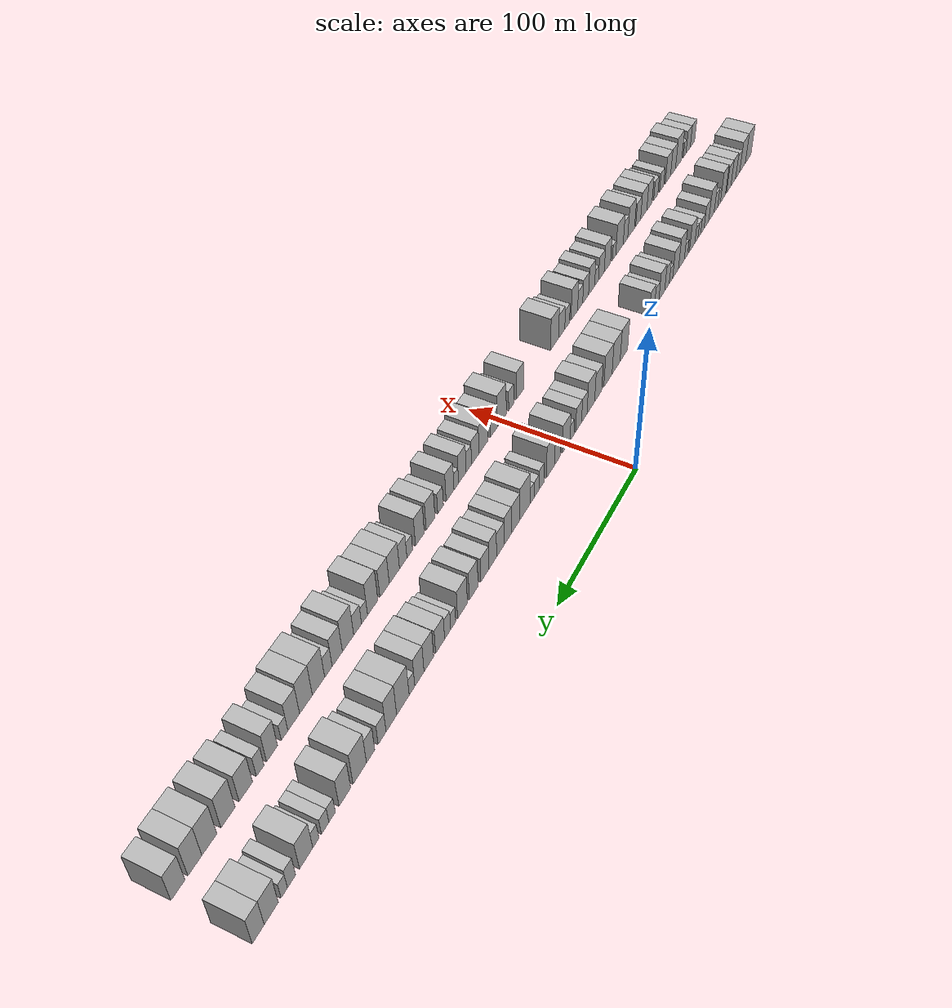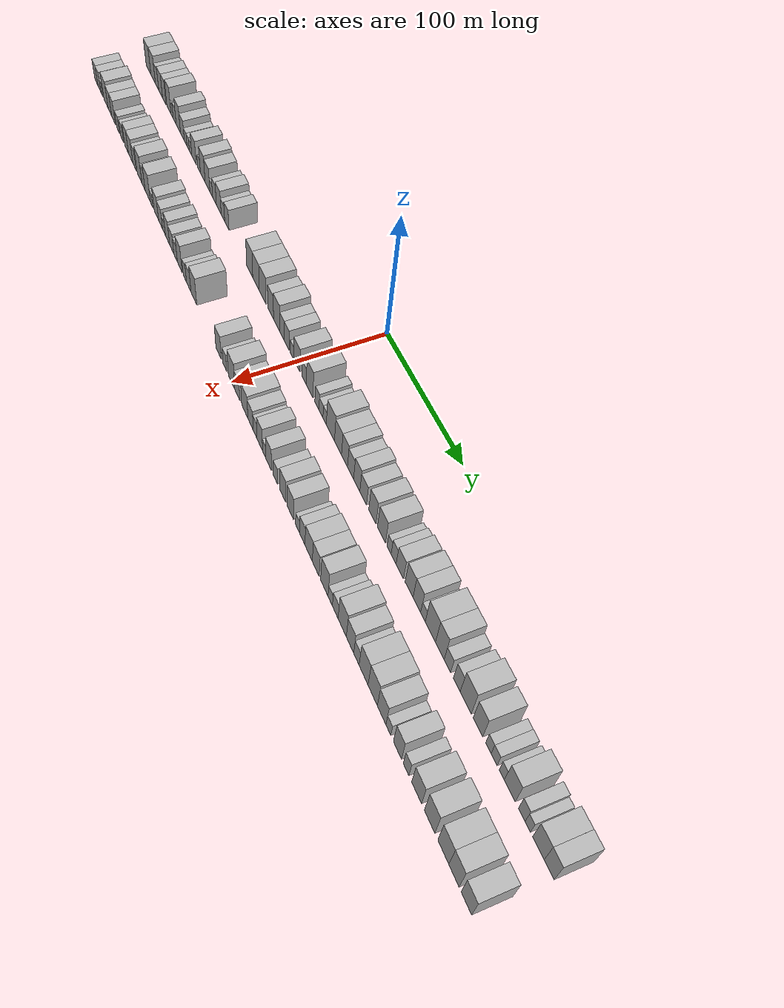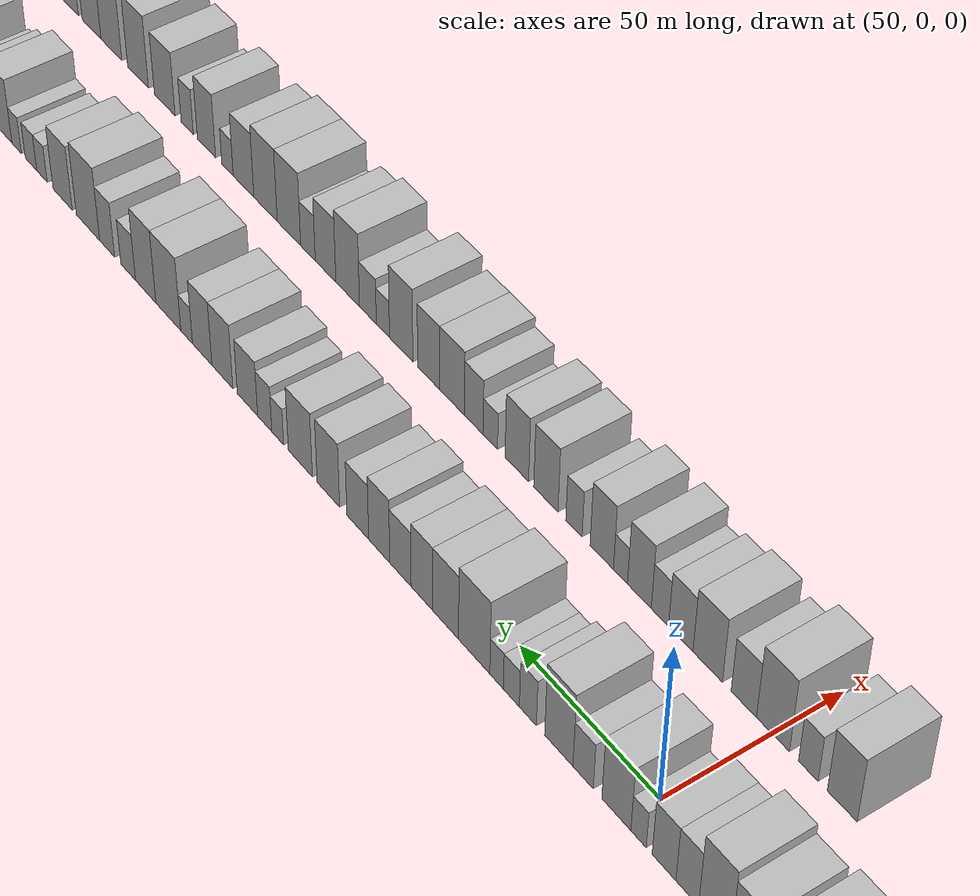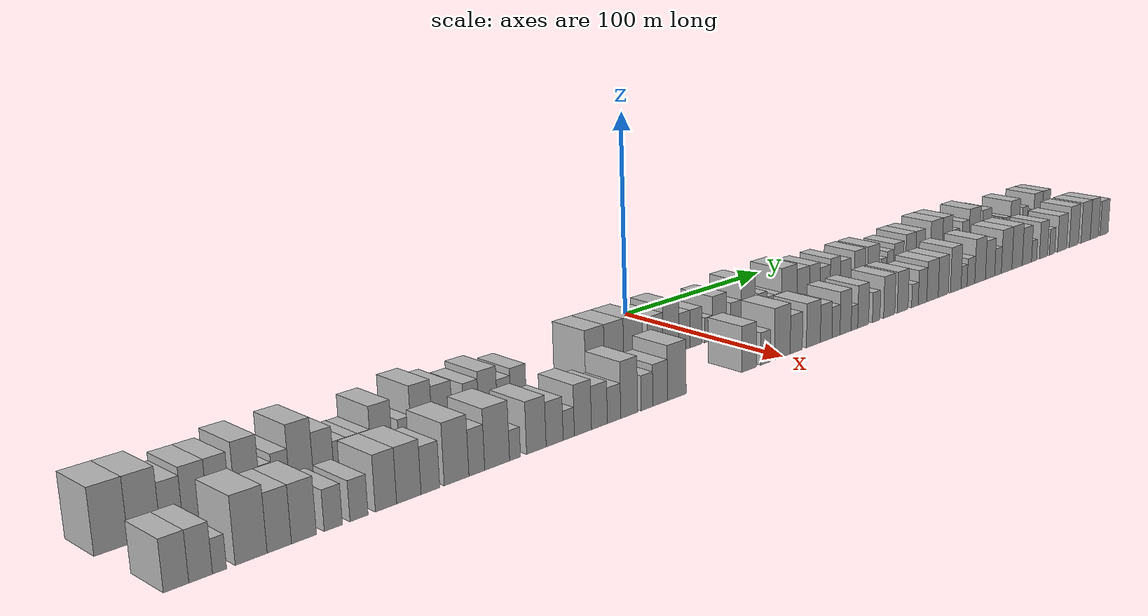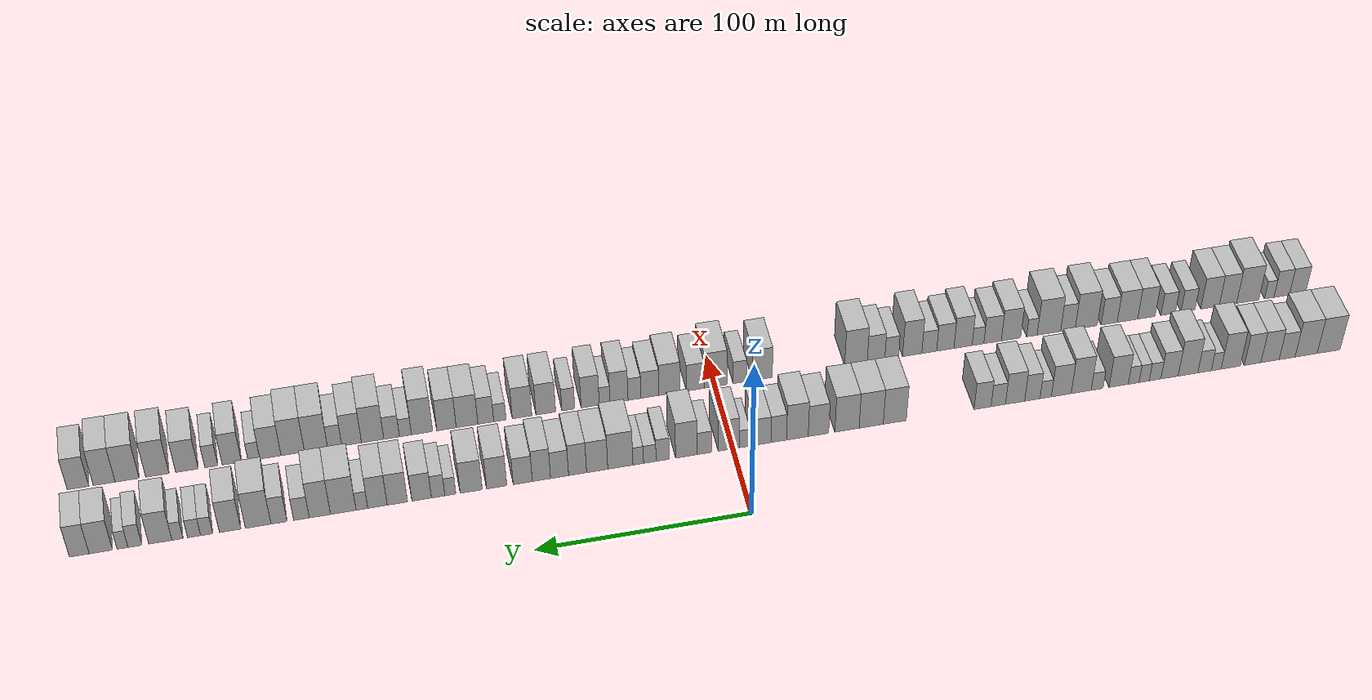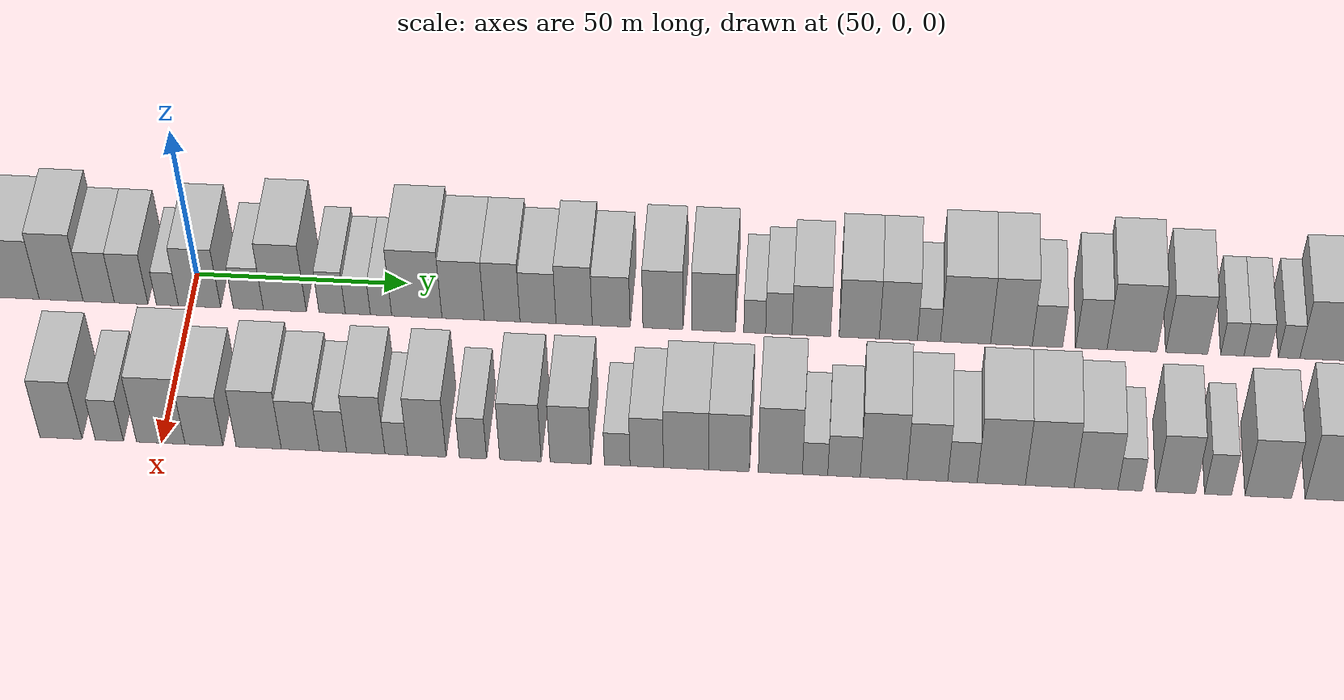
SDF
<sdf version="1.6">
 <world name="default">
  <scene>
   <sky><clouds><speed>12</speed></clouds></sky>
   <ambient>0.4 0.4 0.4 1</ambient>
   <background>0.7 0.7 0.7 1</background>
   <shadows>1</shadows>
  </scene>
  <gravity>0 0 -9.8066</gravity>
  <magnetic_field>6e-06 2.3e-05 -4.2e-05</magnetic_field>
  <physics default="0" name="default_physics" type="ode">
   <ode>
    <solver>
     <type>quick</type>
     <iters>10</iters>
     <sor>1.0</sor>
     <use_dynamic_moi_rescaling>0</use_dynamic_moi_rescaling>
    </solver>
    <constraints>
     <cfm>0</cfm>
     <erp>0.2</erp>
     <contact_max_correcting_vel>100</contact_max_correcting_vel>
     <contact_surface_layer>0.001</contact_surface_layer>
    </constraints>
   </ode>
   <max_step_size>0.004</max_step_size>
   <real_time_factor>1</real_time_factor>
   <real_time_update_rate>250</real_time_update_rate>
  </physics>
  <light name="sun" type="directional">
   <pose>0 0 10 0 0 0</pose>
   <diffuse>0.8 0.8 0.8 1</diffuse>
   <specular>0.2 0.2 0.2 1</specular>
   <attenuation>
    <range>1000</range>
    <constant>0.9</constant>
    <linear>0.01</linear>
    <quadratic>0.001</quadratic>
   </attenuation>
   <direction>-0.5 0.1 -0.9</direction>
  </light>
  <model name="building_1">
   <static>1</static>
   <pose>50.0000 -294.1482 0 0.000000 0.000000 0.000000</pose>
   <link name="link">
    <pose>0 0 12.00 0 0 0</pose>
    <collision name="collision"><geometry><box><size>20.0000 11.7035 24.0000</size></box></geometry></collision>
    <visual name="visual">
     <cast_shadows>0</cast_shadows>
     <geometry><box><size>20.0000 11.7035 24.0000</size></box></geometry>
     <material>
      <script>
       <uri>model://HANNAS_wall/materials/scripts</uri>
       <uri>model://HANNAS_wall/materials/textures</uri>
       <name>vrc/HANNAS_wall</name>
      </script>
     </material>
    </visual>
   </link>
  </model>
  <model name="building_2">
   <static>1</static>
   <pose>50.0000 -282.6605 0 0.000000 0.000000 0.000000</pose>
   <link name="link">
    <pose>0 0 12.00 0 0 0</pose>
    <collision name="collision"><geometry><box><size>20.0000 11.2720 24.0000</size></box></geometry></collision>
    <visual name="visual">
     <cast_shadows>0</cast_shadows>
     <geometry><box><size>20.0000 11.2720 24.0000</size></box></geometry>
     <material>
      <script>
       <uri>model://HANNAS_wall/materials/scripts</uri>
       <uri>model://HANNAS_wall/materials/textures</uri>
       <name>vrc/HANNAS_wall</name>
      </script>
     </material>
    </visual>
   </link>
  </model>
  <model name="building_3">
   <static>1</static>
   <pose>50.0000 -272.9549 0 0.000000 0.000000 0.000000</pose>
   <link name="link">
    <pose>0 0 9.00 0 0 0</pose>
    <collision name="collision"><geometry><box><size>20.0000 8.1390 18.0000</size></box></geometry></collision>
    <visual name="visual">
     <cast_shadows>0</cast_shadows>
     <geometry><box><size>20.0000 8.1390 18.0000</size></box></geometry>
     <material>
      <script>
       <uri>model://HANNAS_wall/materials/scripts</uri>
       <uri>model://HANNAS_wall/materials/textures</uri>
       <name>vrc/HANNAS_wall</name>
      </script>
     </material>
    </visual>
   </link>
  </model>
  <model name="building_4">
   <static>1</static>
   <pose>50.0000 -264.2775 0 0.000000 0.000000 0.000000</pose>
   <link name="link">
    <pose>0 0 10.50 0 0 0</pose>
    <collision name="collision"><geometry><box><size>20.0000 9.2159 21.0000</size></box></geometry></collision>
    <visual name="visual">
     <cast_shadows>0</cast_shadows>
     <geometry><box><size>20.0000 9.2159 21.0000</size></box></geometry>
     <material>
      <script>
       <uri>model://HANNAS_wall/materials/scripts</uri>
       <uri>model://HANNAS_wall/materials/textures</uri>
       <name>vrc/HANNAS_wall</name>
      </script>
     </material>
    </visual>
   </link>
  </model>
  <model name="building_5">
   <static>1</static>
   <pose>50.0000 -255.4613 0 0.000000 0.000000 0.000000</pose>
   <link name="link">
    <pose>0 0 10.50 0 0 0</pose>
    <collision name="collision"><geometry><box><size>20.0000 8.4165 21.0000</size></box></geometry></collision>
    <visual name="visual">
     <cast_shadows>0</cast_shadows>
     <geometry><box><size>20.0000 8.4165 21.0000</size></box></geometry>
     <material>
      <script>
       <uri>model://HANNAS_wall/materials/scripts</uri>
       <uri>model://HANNAS_wall/materials/textures</uri>
       <name>vrc/HANNAS_wall</name>
      </script>
     </material>
    </visual>
   </link>
  </model>
  <model name="building_6">
   <static>1</static>
   <pose>50.0000 -244.3734 0 0.000000 0.000000 0.000000</pose>
   <link name="link">
    <pose>0 0 12.00 0 0 0</pose>
    <collision name="collision"><geometry><box><size>20.0000 9.7594 24.0000</size></box></geometry></collision>
    <visual name="visual">
     <cast_shadows>0</cast_shadows>
     <geometry><box><size>20.0000 9.7594 24.0000</size></box></geometry>
     <material>
      <script>
       <uri>model://HANNAS_wall/materials/scripts</uri>
       <uri>model://HANNAS_wall/materials/textures</uri>
       <name>vrc/HANNAS_wall</name>
      </script>
     </material>
    </visual>
   </link>
  </model>
  <model name="building_7">
   <static>1</static>
   <pose>50.0000 -237.0098 0 0.000000 0.000000 0.000000</pose>
   <link name="link">
    <pose>0 0 6.00 0 0 0</pose>
    <collision name="collision"><geometry><box><size>20.0000 4.9678 12.0000</size></box></geometry></collision>
    <visual name="visual">
     <cast_shadows>0</cast_shadows>
     <geometry><box><size>20.0000 4.9678 12.0000</size></box></geometry>
     <material>
      <script>
       <uri>model://HANNAS_wall/materials/scripts</uri>
       <uri>model://HANNAS_wall/materials/textures</uri>
       <name>vrc/HANNAS_wall</name>
      </script>
     </material>
    </visual>
   </link>
  </model>
  <model name="building_8">
   <static>1</static>
   <pose>50.0000 -231.1403 0 0.000000 0.000000 0.000000</pose>
   <link name="link">
    <pose>0 0 7.50 0 0 0</pose>
    <collision name="collision"><geometry><box><size>20.0000 6.7712 15.0000</size></box></geometry></collision>
    <visual name="visual">
     <cast_shadows>0</cast_shadows>
     <geometry><box><size>20.0000 6.7712 15.0000</size></box></geometry>
     <material>
      <script>
       <uri>model://HANNAS_wall/materials/scripts</uri>
       <uri>model://HANNAS_wall/materials/textures</uri>
       <name>vrc/HANNAS_wall</name>
      </script>
     </material>
    </visual>
   </link>
  </model>
  <model name="building_9">
   <static>1</static>
   <pose>50.0000 -222.8036 0 0.000000 0.000000 0.000000</pose>
   <link name="link">
    <pose>0 0 12.00 0 0 0</pose>
    <collision name="collision"><geometry><box><size>20.0000 9.9022 24.0000</size></box></geometry></collision>
    <visual name="visual">
     <cast_shadows>0</cast_shadows>
     <geometry><box><size>20.0000 9.9022 24.0000</size></box></geometry>
     <material>
      <script>
       <uri>model://HANNAS_wall/materials/scripts</uri>
       <uri>model://HANNAS_wall/materials/textures</uri>
       <name>vrc/HANNAS_wall</name>
      </script>
     </material>
    </visual>
   </link>
  </model>
  <model name="building_10">
   <static>1</static>
   <pose>50.0000 -213.5388 0 0.000000 0.000000 0.000000</pose>
   <link name="link">
    <pose>0 0 9.00 0 0 0</pose>
    <collision name="collision"><geometry><box><size>20.0000 8.6273 18.0000</size></box></geometry></collision>
    <visual name="visual">
     <cast_shadows>0</cast_shadows>
     <geometry><box><size>20.0000 8.6273 18.0000</size></box></geometry>
     <material>
      <script>
       <uri>model://HANNAS_wall/materials/scripts</uri>
       <uri>model://HANNAS_wall/materials/textures</uri>
       <name>vrc/HANNAS_wall</name>
      </script>
     </material>
    </visual>
   </link>
  </model>
  <model name="building_11">
   <static>1</static>
   <pose>50.0000 -206.2895 0 0.000000 0.000000 0.000000</pose>
   <link name="link">
    <pose>0 0 6.00 0 0 0</pose>
    <collision name="collision"><geometry><box><size>20.0000 5.8713 12.0000</size></box></geometry></collision>
    <visual name="visual">
     <cast_shadows>0</cast_shadows>
     <geometry><box><size>20.0000 5.8713 12.0000</size></box></geometry>
     <material>
      <script>
       <uri>model://HANNAS_wall/materials/scripts</uri>
       <uri>model://HANNAS_wall/materials/textures</uri>
       <name>vrc/HANNAS_wall</name>
      </script>
     </material>
    </visual>
   </link>
  </model>
  <model name="building_12">
   <static>1</static>
   <pose>50.0000 -200.8021 0 0.000000 0.000000 0.000000</pose>
   <link name="link">
    <pose>0 0 6.00 0 0 0</pose>
    <collision name="collision"><geometry><box><size>20.0000 5.1035 12.0000</size></box></geometry></collision>
    <visual name="visual">
     <cast_shadows>0</cast_shadows>
     <geometry><box><size>20.0000 5.1035 12.0000</size></box></geometry>
     <material>
      <script>
       <uri>model://HANNAS_wall/materials/scripts</uri>
       <uri>model://HANNAS_wall/materials/textures</uri>
       <name>vrc/HANNAS_wall</name>
      </script>
     </material>
    </visual>
   </link>
  </model>
  <model name="building_13">
   <static>1</static>
   <pose>50.0000 -195.5627 0 0.000000 0.000000 0.000000</pose>
   <link name="link">
    <pose>0 0 6.00 0 0 0</pose>
    <collision name="collision"><geometry><box><size>20.0000 5.3754 12.0000</size></box></geometry></collision>
    <visual name="visual">
     <cast_shadows>0</cast_shadows>
     <geometry><box><size>20.0000 5.3754 12.0000</size></box></geometry>
     <material>
      <script>
       <uri>model://HANNAS_wall/materials/scripts</uri>
       <uri>model://HANNAS_wall/materials/textures</uri>
       <name>vrc/HANNAS_wall</name>
      </script>
     </material>
    </visual>
   </link>
  </model>
  <model name="building_14">
   <static>1</static>
   <pose>50.0000 -188.0589 0 0.000000 0.000000 0.000000</pose>
   <link name="link">
    <pose>0 0 10.50 0 0 0</pose>
    <collision name="collision"><geometry><box><size>20.0000 9.6321 21.0000</size></box></geometry></collision>
    <visual name="visual">
     <cast_shadows>0</cast_shadows>
     <geometry><box><size>20.0000 9.6321 21.0000</size></box></geometry>
     <material>
      <script>
       <uri>model://HANNAS_wall/materials/scripts</uri>
       <uri>model://HANNAS_wall/materials/textures</uri>
       <name>vrc/HANNAS_wall</name>
      </script>
     </material>
    </visual>
   </link>
  </model>
  <model name="building_15">
   <static>1</static>
   <pose>50.0000 -177.3027 0 0.000000 0.000000 0.000000</pose>
   <link name="link">
    <pose>0 0 6.00 0 0 0</pose>
    <collision name="collision"><geometry><box><size>20.0000 5.8805 12.0000</size></box></geometry></collision>
    <visual name="visual">
     <cast_shadows>0</cast_shadows>
     <geometry><box><size>20.0000 5.8805 12.0000</size></box></geometry>
     <material>
      <script>
       <uri>model://HANNAS_wall/materials/scripts</uri>
       <uri>model://HANNAS_wall/materials/textures</uri>
       <name>vrc/HANNAS_wall</name>
      </script>
     </material>
    </visual>
   </link>
  </model>
  <model name="building_16">
   <static>1</static>
   <pose>50.0000 -169.3864 0 0.000000 0.000000 0.000000</pose>
   <link name="link">
    <pose>0 0 12.00 0 0 0</pose>
    <collision name="collision"><geometry><box><size>20.0000 9.9520 24.0000</size></box></geometry></collision>
    <visual name="visual">
     <cast_shadows>0</cast_shadows>
     <geometry><box><size>20.0000 9.9520 24.0000</size></box></geometry>
     <material>
      <script>
       <uri>model://HANNAS_wall/materials/scripts</uri>
       <uri>model://HANNAS_wall/materials/textures</uri>
       <name>vrc/HANNAS_wall</name>
      </script>
     </material>
    </visual>
   </link>
  </model>
  <model name="building_17">
   <static>1</static>
   <pose>50.0000 -159.4956 0 0.000000 0.000000 0.000000</pose>
   <link name="link">
    <pose>0 0 10.50 0 0 0</pose>
    <collision name="collision"><geometry><box><size>20.0000 9.8298 21.0000</size></box></geometry></collision>
    <visual name="visual">
     <cast_shadows>0</cast_shadows>
     <geometry><box><size>20.0000 9.8298 21.0000</size></box></geometry>
     <material>
      <script>
       <uri>model://HANNAS_wall/materials/scripts</uri>
       <uri>model://HANNAS_wall/materials/textures</uri>
       <name>vrc/HANNAS_wall</name>
      </script>
     </material>
    </visual>
   </link>
  </model>
  <model name="building_18">
   <static>1</static>
   <pose>50.0000 -151.7910 0 0.000000 0.000000 0.000000</pose>
   <link name="link">
    <pose>0 0 6.00 0 0 0</pose>
    <collision name="collision"><geometry><box><size>20.0000 5.5794 12.0000</size></box></geometry></collision>
    <visual name="visual">
     <cast_shadows>0</cast_shadows>
     <geometry><box><size>20.0000 5.5794 12.0000</size></box></geometry>
     <material>
      <script>
       <uri>model://HANNAS_wall/materials/scripts</uri>
       <uri>model://HANNAS_wall/materials/textures</uri>
       <name>vrc/HANNAS_wall</name>
      </script>
     </material>
    </visual>
   </link>
  </model>
  <model name="building_19">
   <static>1</static>
   <pose>50.0000 -145.2090 0 0.000000 0.000000 0.000000</pose>
   <link name="link">
    <pose>0 0 9.00 0 0 0</pose>
    <collision name="collision"><geometry><box><size>20.0000 7.5845 18.0000</size></box></geometry></collision>
    <visual name="visual">
     <cast_shadows>0</cast_shadows>
     <geometry><box><size>20.0000 7.5845 18.0000</size></box></geometry>
     <material>
      <script>
       <uri>model://HANNAS_wall/materials/scripts</uri>
       <uri>model://HANNAS_wall/materials/textures</uri>
       <name>vrc/HANNAS_wall</name>
      </script>
     </material>
    </visual>
   </link>
  </model>
  <model name="building_20">
   <static>1</static>
   <pose>50.0000 -136.6767 0 0.000000 0.000000 0.000000</pose>
   <link name="link">
    <pose>0 0 10.50 0 0 0</pose>
    <collision name="collision"><geometry><box><size>20.0000 9.4801 21.0000</size></box></geometry></collision>
    <visual name="visual">
     <cast_shadows>0</cast_shadows>
     <geometry><box><size>20.0000 9.4801 21.0000</size></box></geometry>
     <material>
      <script>
       <uri>model://HANNAS_wall/materials/scripts</uri>
       <uri>model://HANNAS_wall/materials/textures</uri>
       <name>vrc/HANNAS_wall</name>
      </script>
     </material>
    </visual>
   </link>
  </model>
  <model name="building_21">
   <static>1</static>
   <pose>50.0000 -128.4001 0 0.000000 0.000000 0.000000</pose>
   <link name="link">
    <pose>0 0 7.50 0 0 0</pose>
    <collision name="collision"><geometry><box><size>20.0000 7.0731 15.0000</size></box></geometry></collision>
    <visual name="visual">
     <cast_shadows>0</cast_shadows>
     <geometry><box><size>20.0000 7.0731 15.0000</size></box></geometry>
     <material>
      <script>
       <uri>model://HANNAS_wall/materials/scripts</uri>
       <uri>model://HANNAS_wall/materials/textures</uri>
       <name>vrc/HANNAS_wall</name>
      </script>
     </material>
    </visual>
   </link>
  </model>
  <model name="building_22">
   <static>1</static>
   <pose>50.0000 -120.6991 0 0.000000 0.000000 0.000000</pose>
   <link name="link">
    <pose>0 0 9.00 0 0 0</pose>
    <collision name="collision"><geometry><box><size>20.0000 8.3287 18.0000</size></box></geometry></collision>
    <visual name="visual">
     <cast_shadows>0</cast_shadows>
     <geometry><box><size>20.0000 8.3287 18.0000</size></box></geometry>
     <material>
      <script>
       <uri>model://HANNAS_wall/materials/scripts</uri>
       <uri>model://HANNAS_wall/materials/textures</uri>
       <name>vrc/HANNAS_wall</name>
      </script>
     </material>
    </visual>
   </link>
  </model>
  <model name="building_23">
   <static>1</static>
   <pose>50.0000 -77.7936 0 0.000000 0.000000 0.000000</pose>
   <link name="link">
    <pose>0 0 12.00 0 0 0</pose>
    <collision name="collision"><geometry><box><size>20.0000 11.1608 24.0000</size></box></geometry></collision>
    <visual name="visual">
     <cast_shadows>0</cast_shadows>
     <geometry><box><size>20.0000 11.1608 24.0000</size></box></geometry>
     <material>
      <script>
       <uri>model://HANNAS_wall/materials/scripts</uri>
       <uri>model://HANNAS_wall/materials/textures</uri>
       <name>vrc/HANNAS_wall</name>
      </script>
     </material>
    </visual>
   </link>
  </model>
  <model name="building_24">
   <static>1</static>
   <pose>50.0000 -66.3565 0 0.000000 0.000000 0.000000</pose>
   <link name="link">
    <pose>0 0 12.00 0 0 0</pose>
    <collision name="collision"><geometry><box><size>20.0000 11.7134 24.0000</size></box></geometry></collision>
    <visual name="visual">
     <cast_shadows>0</cast_shadows>
     <geometry><box><size>20.0000 11.7134 24.0000</size></box></geometry>
     <material>
      <script>
       <uri>model://HANNAS_wall/materials/scripts</uri>
       <uri>model://HANNAS_wall/materials/textures</uri>
       <name>vrc/HANNAS_wall</name>
      </script>
     </material>
    </visual>
   </link>
  </model>
  <model name="building_25">
   <static>1</static>
   <pose>50.0000 -54.6394 0 0.000000 0.000000 0.000000</pose>
   <link name="link">
    <pose>0 0 12.00 0 0 0</pose>
    <collision name="collision"><geometry><box><size>20.0000 11.7207 24.0000</size></box></geometry></collision>
    <visual name="visual">
     <cast_shadows>0</cast_shadows>
     <geometry><box><size>20.0000 11.7207 24.0000</size></box></geometry>
     <material>
      <script>
       <uri>model://HANNAS_wall/materials/scripts</uri>
       <uri>model://HANNAS_wall/materials/textures</uri>
       <name>vrc/HANNAS_wall</name>
      </script>
     </material>
    </visual>
   </link>
  </model>
  <model name="building_26">
   <static>1</static>
   <pose>50.0000 -40.8496 0 0.000000 0.000000 0.000000</pose>
   <link name="link">
    <pose>0 0 10.50 0 0 0</pose>
    <collision name="collision"><geometry><box><size>20.0000 9.8590 21.0000</size></box></geometry></collision>
    <visual name="visual">
     <cast_shadows>0</cast_shadows>
     <geometry><box><size>20.0000 9.8590 21.0000</size></box></geometry>
     <material>
      <script>
       <uri>model://HANNAS_wall/materials/scripts</uri>
       <uri>model://HANNAS_wall/materials/textures</uri>
       <name>vrc/HANNAS_wall</name>
      </script>
     </material>
    </visual>
   </link>
  </model>
  <model name="building_27">
   <static>1</static>
   <pose>50.0000 -30.7052 0 0.000000 0.000000 0.000000</pose>
   <link name="link">
    <pose>0 0 12.00 0 0 0</pose>
    <collision name="collision"><geometry><box><size>20.0000 10.4298 24.0000</size></box></geometry></collision>
    <visual name="visual">
     <cast_shadows>0</cast_shadows>
     <geometry><box><size>20.0000 10.4298 24.0000</size></box></geometry>
     <material>
      <script>
       <uri>model://HANNAS_wall/materials/scripts</uri>
       <uri>model://HANNAS_wall/materials/textures</uri>
       <name>vrc/HANNAS_wall</name>
      </script>
     </material>
    </visual>
   </link>
  </model>
  <model name="building_28">
   <static>1</static>
   <pose>50.0000 -21.7638 0 0.000000 0.000000 0.000000</pose>
   <link name="link">
    <pose>0 0 9.00 0 0 0</pose>
    <collision name="collision"><geometry><box><size>20.0000 7.4530 18.0000</size></box></geometry></collision>
    <visual name="visual">
     <cast_shadows>0</cast_shadows>
     <geometry><box><size>20.0000 7.4530 18.0000</size></box></geometry>
     <material>
      <script>
       <uri>model://HANNAS_wall/materials/scripts</uri>
       <uri>model://HANNAS_wall/materials/textures</uri>
       <name>vrc/HANNAS_wall</name>
      </script>
     </material>
    </visual>
   </link>
  </model>
  <model name="building_29">
   <static>1</static>
   <pose>50.0000 -14.0712 0 0.000000 0.000000 0.000000</pose>
   <link name="link">
    <pose>0 0 9.00 0 0 0</pose>
    <collision name="collision"><geometry><box><size>20.0000 7.9321 18.0000</size></box></geometry></collision>
    <visual name="visual">
     <cast_shadows>0</cast_shadows>
     <geometry><box><size>20.0000 7.9321 18.0000</size></box></geometry>
     <material>
      <script>
       <uri>model://HANNAS_wall/materials/scripts</uri>
       <uri>model://HANNAS_wall/materials/textures</uri>
       <name>vrc/HANNAS_wall</name>
      </script>
     </material>
    </visual>
   </link>
  </model>
  <model name="building_30">
   <static>1</static>
   <pose>50.0000 -5.4879 0 0.000000 0.000000 0.000000</pose>
   <link name="link">
    <pose>0 0 6.00 0 0 0</pose>
    <collision name="collision"><geometry><box><size>20.0000 5.2346 12.0000</size></box></geometry></collision>
    <visual name="visual">
     <cast_shadows>0</cast_shadows>
     <geometry><box><size>20.0000 5.2346 12.0000</size></box></geometry>
     <material>
      <script>
       <uri>model://HANNAS_wall/materials/scripts</uri>
       <uri>model://HANNAS_wall/materials/textures</uri>
       <name>vrc/HANNAS_wall</name>
      </script>
     </material>
    </visual>
   </link>
  </model>
  <model name="building_31">
   <static>1</static>
   <pose>50.0000 2.1301 0 0.000000 0.000000 0.000000</pose>
   <link name="link">
    <pose>0 0 10.50 0 0 0</pose>
    <collision name="collision"><geometry><box><size>20.0000 10.0014 21.0000</size></box></geometry></collision>
    <visual name="visual">
     <cast_shadows>0</cast_shadows>
     <geometry><box><size>20.0000 10.0014 21.0000</size></box></geometry>
     <material>
      <script>
       <uri>model://HANNAS_wall/materials/scripts</uri>
       <uri>model://HANNAS_wall/materials/textures</uri>
       <name>vrc/HANNAS_wall</name>
      </script>
     </material>
    </visual>
   </link>
  </model>
  <model name="building_32">
   <static>1</static>
   <pose>50.0000 13.6980 0 0.000000 0.000000 0.000000</pose>
   <link name="link">
    <pose>0 0 7.50 0 0 0</pose>
    <collision name="collision"><geometry><box><size>20.0000 7.1344 15.0000</size></box></geometry></collision>
    <visual name="visual">
     <cast_shadows>0</cast_shadows>
     <geometry><box><size>20.0000 7.1344 15.0000</size></box></geometry>
     <material>
      <script>
       <uri>model://HANNAS_wall/materials/scripts</uri>
       <uri>model://HANNAS_wall/materials/textures</uri>
       <name>vrc/HANNAS_wall</name>
      </script>
     </material>
    </visual>
   </link>
  </model>
  <model name="building_33">
   <static>1</static>
   <pose>50.0000 22.3238 0 0.000000 0.000000 0.000000</pose>
   <link name="link">
    <pose>0 0 12.00 0 0 0</pose>
    <collision name="collision"><geometry><box><size>20.0000 10.1171 24.0000</size></box></geometry></collision>
    <visual name="visual">
     <cast_shadows>0</cast_shadows>
     <geometry><box><size>20.0000 10.1171 24.0000</size></box></geometry>
     <material>
      <script>
       <uri>model://HANNAS_wall/materials/scripts</uri>
       <uri>model://HANNAS_wall/materials/textures</uri>
       <name>vrc/HANNAS_wall</name>
      </script>
     </material>
    </visual>
   </link>
  </model>
  <model name="building_34">
   <static>1</static>
   <pose>50.0000 33.4924 0 0.000000 0.000000 0.000000</pose>
   <link name="link">
    <pose>0 0 7.50 0 0 0</pose>
    <collision name="collision"><geometry><box><size>20.0000 6.2201 15.0000</size></box></geometry></collision>
    <visual name="visual">
     <cast_shadows>0</cast_shadows>
     <geometry><box><size>20.0000 6.2201 15.0000</size></box></geometry>
     <material>
      <script>
       <uri>model://HANNAS_wall/materials/scripts</uri>
       <uri>model://HANNAS_wall/materials/textures</uri>
       <name>vrc/HANNAS_wall</name>
      </script>
     </material>
    </visual>
   </link>
  </model>
  <model name="building_35">
   <static>1</static>
   <pose>50.0000 39.5580 0 0.000000 0.000000 0.000000</pose>
   <link name="link">
    <pose>0 0 6.00 0 0 0</pose>
    <collision name="collision"><geometry><box><size>20.0000 5.9111 12.0000</size></box></geometry></collision>
    <visual name="visual">
     <cast_shadows>0</cast_shadows>
     <geometry><box><size>20.0000 5.9111 12.0000</size></box></geometry>
     <material>
      <script>
       <uri>model://HANNAS_wall/materials/scripts</uri>
       <uri>model://HANNAS_wall/materials/textures</uri>
       <name>vrc/HANNAS_wall</name>
      </script>
     </material>
    </visual>
   </link>
  </model>
  <model name="building_36">
   <static>1</static>
   <pose>50.0000 45.0231 0 0.000000 0.000000 0.000000</pose>
   <link name="link">
    <pose>0 0 6.00 0 0 0</pose>
    <collision name="collision"><geometry><box><size>20.0000 5.0190 12.0000</size></box></geometry></collision>
    <visual name="visual">
     <cast_shadows>0</cast_shadows>
     <geometry><box><size>20.0000 5.0190 12.0000</size></box></geometry>
     <material>
      <script>
       <uri>model://HANNAS_wall/materials/scripts</uri>
       <uri>model://HANNAS_wall/materials/textures</uri>
       <name>vrc/HANNAS_wall</name>
      </script>
     </material>
    </visual>
   </link>
  </model>
  <model name="building_37">
   <static>1</static>
   <pose>50.0000 53.4516 0 0.000000 0.000000 0.000000</pose>
   <link name="link">
    <pose>0 0 12.00 0 0 0</pose>
    <collision name="collision"><geometry><box><size>20.0000 11.8379 24.0000</size></box></geometry></collision>
    <visual name="visual">
     <cast_shadows>0</cast_shadows>
     <geometry><box><size>20.0000 11.8379 24.0000</size></box></geometry>
     <material>
      <script>
       <uri>model://HANNAS_wall/materials/scripts</uri>
       <uri>model://HANNAS_wall/materials/textures</uri>
       <name>vrc/HANNAS_wall</name>
      </script>
     </material>
    </visual>
   </link>
  </model>
  <model name="building_38">
   <static>1</static>
   <pose>50.0000 64.3555 0 0.000000 0.000000 0.000000</pose>
   <link name="link">
    <pose>0 0 10.50 0 0 0</pose>
    <collision name="collision"><geometry><box><size>20.0000 9.9698 21.0000</size></box></geometry></collision>
    <visual name="visual">
     <cast_shadows>0</cast_shadows>
     <geometry><box><size>20.0000 9.9698 21.0000</size></box></geometry>
     <material>
      <script>
       <uri>model://HANNAS_wall/materials/scripts</uri>
       <uri>model://HANNAS_wall/materials/textures</uri>
       <name>vrc/HANNAS_wall</name>
      </script>
     </material>
    </visual>
   </link>
  </model>
  <model name="building_39">
   <static>1</static>
   <pose>50.0000 73.5436 0 0.000000 0.000000 0.000000</pose>
   <link name="link">
    <pose>0 0 10.50 0 0 0</pose>
    <collision name="collision"><geometry><box><size>20.0000 8.4065 21.0000</size></box></geometry></collision>
    <visual name="visual">
     <cast_shadows>0</cast_shadows>
     <geometry><box><size>20.0000 8.4065 21.0000</size></box></geometry>
     <material>
      <script>
       <uri>model://HANNAS_wall/materials/scripts</uri>
       <uri>model://HANNAS_wall/materials/textures</uri>
       <name>vrc/HANNAS_wall</name>
      </script>
     </material>
    </visual>
   </link>
  </model>
  <model name="building_40">
   <static>1</static>
   <pose>50.0000 81.9628 0 0.000000 0.000000 0.000000</pose>
   <link name="link">
    <pose>0 0 9.00 0 0 0</pose>
    <collision name="collision"><geometry><box><size>20.0000 8.4319 18.0000</size></box></geometry></collision>
    <visual name="visual">
     <cast_shadows>0</cast_shadows>
     <geometry><box><size>20.0000 8.4319 18.0000</size></box></geometry>
     <material>
      <script>
       <uri>model://HANNAS_wall/materials/scripts</uri>
       <uri>model://HANNAS_wall/materials/textures</uri>
       <name>vrc/HANNAS_wall</name>
      </script>
     </material>
    </visual>
   </link>
  </model>
  <model name="building_41">
   <static>1</static>
   <pose>50.0000 90.4274 0 0.000000 0.000000 0.000000</pose>
   <link name="link">
    <pose>0 0 10.50 0 0 0</pose>
    <collision name="collision"><geometry><box><size>20.0000 8.4972 21.0000</size></box></geometry></collision>
    <visual name="visual">
     <cast_shadows>0</cast_shadows>
     <geometry><box><size>20.0000 8.4972 21.0000</size></box></geometry>
     <material>
      <script>
       <uri>model://HANNAS_wall/materials/scripts</uri>
       <uri>model://HANNAS_wall/materials/textures</uri>
       <name>vrc/HANNAS_wall</name>
      </script>
     </material>
    </visual>
   </link>
  </model>
  <model name="building_42">
   <static>1</static>
   <pose>50.0000 99.1156 0 0.000000 0.000000 0.000000</pose>
   <link name="link">
    <pose>0 0 9.00 0 0 0</pose>
    <collision name="collision"><geometry><box><size>20.0000 8.8792 18.0000</size></box></geometry></collision>
    <visual name="visual">
     <cast_shadows>0</cast_shadows>
     <geometry><box><size>20.0000 8.8792 18.0000</size></box></geometry>
     <material>
      <script>
       <uri>model://HANNAS_wall/materials/scripts</uri>
       <uri>model://HANNAS_wall/materials/textures</uri>
       <name>vrc/HANNAS_wall</name>
      </script>
     </material>
    </visual>
   </link>
  </model>
  <model name="building_43">
   <static>1</static>
   <pose>50.0000 111.2433 0 0.000000 0.000000 0.000000</pose>
   <link name="link">
    <pose>0 0 10.50 0 0 0</pose>
    <collision name="collision"><geometry><box><size>20.0000 9.3763 21.0000</size></box></geometry></collision>
    <visual name="visual">
     <cast_shadows>0</cast_shadows>
     <geometry><box><size>20.0000 9.3763 21.0000</size></box></geometry>
     <material>
      <script>
       <uri>model://HANNAS_wall/materials/scripts</uri>
       <uri>model://HANNAS_wall/materials/textures</uri>
       <name>vrc/HANNAS_wall</name>
      </script>
     </material>
    </visual>
   </link>
  </model>
  <model name="building_44">
   <static>1</static>
   <pose>50.0000 123.0411 0 0.000000 0.000000 0.000000</pose>
   <link name="link">
    <pose>0 0 10.50 0 0 0</pose>
    <collision name="collision"><geometry><box><size>20.0000 10.2192 21.0000</size></box></geometry></collision>
    <visual name="visual">
     <cast_shadows>0</cast_shadows>
     <geometry><box><size>20.0000 10.2192 21.0000</size></box></geometry>
     <material>
      <script>
       <uri>model://HANNAS_wall/materials/scripts</uri>
       <uri>model://HANNAS_wall/materials/textures</uri>
       <name>vrc/HANNAS_wall</name>
      </script>
     </material>
    </visual>
   </link>
  </model>
  <model name="building_45">
   <static>1</static>
   <pose>50.0000 132.7010 0 0.000000 0.000000 0.000000</pose>
   <link name="link">
    <pose>0 0 6.00 0 0 0</pose>
    <collision name="collision"><geometry><box><size>20.0000 5.1006 12.0000</size></box></geometry></collision>
    <visual name="visual">
     <cast_shadows>0</cast_shadows>
     <geometry><box><size>20.0000 5.1006 12.0000</size></box></geometry>
     <material>
      <script>
       <uri>model://HANNAS_wall/materials/scripts</uri>
       <uri>model://HANNAS_wall/materials/textures</uri>
       <name>vrc/HANNAS_wall</name>
      </script>
     </material>
    </visual>
   </link>
  </model>
  <model name="building_46">
   <static>1</static>
   <pose>50.0000 138.3369 0 0.000000 0.000000 0.000000</pose>
   <link name="link">
    <pose>0 0 7.50 0 0 0</pose>
    <collision name="collision"><geometry><box><size>20.0000 6.1713 15.0000</size></box></geometry></collision>
    <visual name="visual">
     <cast_shadows>0</cast_shadows>
     <geometry><box><size>20.0000 6.1713 15.0000</size></box></geometry>
     <material>
      <script>
       <uri>model://HANNAS_wall/materials/scripts</uri>
       <uri>model://HANNAS_wall/materials/textures</uri>
       <name>vrc/HANNAS_wall</name>
      </script>
     </material>
    </visual>
   </link>
  </model>
  <model name="building_47">
   <static>1</static>
   <pose>50.0000 145.9093 0 0.000000 0.000000 0.000000</pose>
   <link name="link">
    <pose>0 0 9.00 0 0 0</pose>
    <collision name="collision"><geometry><box><size>20.0000 8.9736 18.0000</size></box></geometry></collision>
    <visual name="visual">
     <cast_shadows>0</cast_shadows>
     <geometry><box><size>20.0000 8.9736 18.0000</size></box></geometry>
     <material>
      <script>
       <uri>model://HANNAS_wall/materials/scripts</uri>
       <uri>model://HANNAS_wall/materials/textures</uri>
       <name>vrc/HANNAS_wall</name>
      </script>
     </material>
    </visual>
   </link>
  </model>
  <model name="building_48">
   <static>1</static>
   <pose>50.0000 157.0753 0 0.000000 0.000000 0.000000</pose>
   <link name="link">
    <pose>0 0 10.50 0 0 0</pose>
    <collision name="collision"><geometry><box><size>20.0000 9.3584 21.0000</size></box></geometry></collision>
    <visual name="visual">
     <cast_shadows>0</cast_shadows>
     <geometry><box><size>20.0000 9.3584 21.0000</size></box></geometry>
     <material>
      <script>
       <uri>model://HANNAS_wall/materials/scripts</uri>
       <uri>model://HANNAS_wall/materials/textures</uri>
       <name>vrc/HANNAS_wall</name>
      </script>
     </material>
    </visual>
   </link>
  </model>
  <model name="building_49">
   <static>1</static>
   <pose>50.0000 166.1852 0 0.000000 0.000000 0.000000</pose>
   <link name="link">
    <pose>0 0 10.50 0 0 0</pose>
    <collision name="collision"><geometry><box><size>20.0000 8.8613 21.0000</size></box></geometry></collision>
    <visual name="visual">
     <cast_shadows>0</cast_shadows>
     <geometry><box><size>20.0000 8.8613 21.0000</size></box></geometry>
     <material>
      <script>
       <uri>model://HANNAS_wall/materials/scripts</uri>
       <uri>model://HANNAS_wall/materials/textures</uri>
       <name>vrc/HANNAS_wall</name>
      </script>
     </material>
    </visual>
   </link>
  </model>
  <model name="building_50">
   <static>1</static>
   <pose>50.0000 173.2969 0 0.000000 0.000000 0.000000</pose>
   <link name="link">
    <pose>0 0 6.00 0 0 0</pose>
    <collision name="collision"><geometry><box><size>20.0000 5.3621 12.0000</size></box></geometry></collision>
    <visual name="visual">
     <cast_shadows>0</cast_shadows>
     <geometry><box><size>20.0000 5.3621 12.0000</size></box></geometry>
     <material>
      <script>
       <uri>model://HANNAS_wall/materials/scripts</uri>
       <uri>model://HANNAS_wall/materials/textures</uri>
       <name>vrc/HANNAS_wall</name>
      </script>
     </material>
    </visual>
   </link>
  </model>
  <model name="building_51">
   <static>1</static>
   <pose>50.0000 181.8073 0 0.000000 0.000000 0.000000</pose>
   <link name="link">
    <pose>0 0 12.00 0 0 0</pose>
    <collision name="collision"><geometry><box><size>20.0000 11.6588 24.0000</size></box></geometry></collision>
    <visual name="visual">
     <cast_shadows>0</cast_shadows>
     <geometry><box><size>20.0000 11.6588 24.0000</size></box></geometry>
     <material>
      <script>
       <uri>model://HANNAS_wall/materials/scripts</uri>
       <uri>model://HANNAS_wall/materials/textures</uri>
       <name>vrc/HANNAS_wall</name>
      </script>
     </material>
    </visual>
   </link>
  </model>
  <model name="building_52">
   <static>1</static>
   <pose>50.0000 192.4684 0 0.000000 0.000000 0.000000</pose>
   <link name="link">
    <pose>0 0 12.00 0 0 0</pose>
    <collision name="collision"><geometry><box><size>20.0000 9.6633 24.0000</size></box></geometry></collision>
    <visual name="visual">
     <cast_shadows>0</cast_shadows>
     <geometry><box><size>20.0000 9.6633 24.0000</size></box></geometry>
     <material>
      <script>
       <uri>model://HANNAS_wall/materials/scripts</uri>
       <uri>model://HANNAS_wall/materials/textures</uri>
       <name>vrc/HANNAS_wall</name>
      </script>
     </material>
    </visual>
   </link>
  </model>
  <model name="building_53">
   <static>1</static>
   <pose>50.0000 200.8308 0 0.000000 0.000000 0.000000</pose>
   <link name="link">
    <pose>0 0 7.50 0 0 0</pose>
    <collision name="collision"><geometry><box><size>20.0000 7.0615 15.0000</size></box></geometry></collision>
    <visual name="visual">
     <cast_shadows>0</cast_shadows>
     <geometry><box><size>20.0000 7.0615 15.0000</size></box></geometry>
     <material>
      <script>
       <uri>model://HANNAS_wall/materials/scripts</uri>
       <uri>model://HANNAS_wall/materials/textures</uri>
       <name>vrc/HANNAS_wall</name>
      </script>
     </material>
    </visual>
   </link>
  </model>
  <model name="building_54">
   <static>1</static>
   <pose>50.0000 210.9991 0 0.000000 0.000000 0.000000</pose>
   <link name="link">
    <pose>0 0 9.00 0 0 0</pose>
    <collision name="collision"><geometry><box><size>20.0000 7.2751 18.0000</size></box></geometry></collision>
    <visual name="visual">
     <cast_shadows>0</cast_shadows>
     <geometry><box><size>20.0000 7.2751 18.0000</size></box></geometry>
     <material>
      <script>
       <uri>model://HANNAS_wall/materials/scripts</uri>
       <uri>model://HANNAS_wall/materials/textures</uri>
       <name>vrc/HANNAS_wall</name>
      </script>
     </material>
    </visual>
   </link>
  </model>
  <model name="building_55">
   <static>1</static>
   <pose>50.0000 220.4315 0 0.000000 0.000000 0.000000</pose>
   <link name="link">
    <pose>0 0 12.00 0 0 0</pose>
    <collision name="collision"><geometry><box><size>20.0000 11.5898 24.0000</size></box></geometry></collision>
    <visual name="visual">
     <cast_shadows>0</cast_shadows>
     <geometry><box><size>20.0000 11.5898 24.0000</size></box></geometry>
     <material>
      <script>
       <uri>model://HANNAS_wall/materials/scripts</uri>
       <uri>model://HANNAS_wall/materials/textures</uri>
       <name>vrc/HANNAS_wall</name>
      </script>
     </material>
    </visual>
   </link>
  </model>
  <model name="building_56">
   <static>1</static>
   <pose>50.0000 233.0825 0 0.000000 0.000000 0.000000</pose>
   <link name="link">
    <pose>0 0 10.50 0 0 0</pose>
    <collision name="collision"><geometry><box><size>20.0000 9.7122 21.0000</size></box></geometry></collision>
    <visual name="visual">
     <cast_shadows>0</cast_shadows>
     <geometry><box><size>20.0000 9.7122 21.0000</size></box></geometry>
     <material>
      <script>
       <uri>model://HANNAS_wall/materials/scripts</uri>
       <uri>model://HANNAS_wall/materials/textures</uri>
       <name>vrc/HANNAS_wall</name>
      </script>
     </material>
    </visual>
   </link>
  </model>
  <model name="building_57">
   <static>1</static>
   <pose>50.0000 243.6332 0 0.000000 0.000000 0.000000</pose>
   <link name="link">
    <pose>0 0 6.00 0 0 0</pose>
    <collision name="collision"><geometry><box><size>20.0000 5.3892 12.0000</size></box></geometry></collision>
    <visual name="visual">
     <cast_shadows>0</cast_shadows>
     <geometry><box><size>20.0000 5.3892 12.0000</size></box></geometry>
     <material>
      <script>
       <uri>model://HANNAS_wall/materials/scripts</uri>
       <uri>model://HANNAS_wall/materials/textures</uri>
       <name>vrc/HANNAS_wall</name>
      </script>
     </material>
    </visual>
   </link>
  </model>
  <model name="building_58">
   <static>1</static>
   <pose>50.0000 249.2939 0 0.000000 0.000000 0.000000</pose>
   <link name="link">
    <pose>0 0 6.00 0 0 0</pose>
    <collision name="collision"><geometry><box><size>20.0000 5.9321 12.0000</size></box></geometry></collision>
    <visual name="visual">
     <cast_shadows>0</cast_shadows>
     <geometry><box><size>20.0000 5.9321 12.0000</size></box></geometry>
     <material>
      <script>
       <uri>model://HANNAS_wall/materials/scripts</uri>
       <uri>model://HANNAS_wall/materials/textures</uri>
       <name>vrc/HANNAS_wall</name>
      </script>
     </material>
    </visual>
   </link>
  </model>
  <model name="building_59">
   <static>1</static>
   <pose>50.0000 256.7350 0 0.000000 0.000000 0.000000</pose>
   <link name="link">
    <pose>0 0 6.00 0 0 0</pose>
    <collision name="collision"><geometry><box><size>20.0000 4.9502 12.0000</size></box></geometry></collision>
    <visual name="visual">
     <cast_shadows>0</cast_shadows>
     <geometry><box><size>20.0000 4.9502 12.0000</size></box></geometry>
     <material>
      <script>
       <uri>model://HANNAS_wall/materials/scripts</uri>
       <uri>model://HANNAS_wall/materials/textures</uri>
       <name>vrc/HANNAS_wall</name>
      </script>
     </material>
    </visual>
   </link>
  </model>
  <model name="building_60">
   <static>1</static>
   <pose>50.0000 264.3996 0 0.000000 0.000000 0.000000</pose>
   <link name="link">
    <pose>0 0 10.50 0 0 0</pose>
    <collision name="collision"><geometry><box><size>20.0000 10.3790 21.0000</size></box></geometry></collision>
    <visual name="visual">
     <cast_shadows>0</cast_shadows>
     <geometry><box><size>20.0000 10.3790 21.0000</size></box></geometry>
     <material>
      <script>
       <uri>model://HANNAS_wall/materials/scripts</uri>
       <uri>model://HANNAS_wall/materials/textures</uri>
       <name>vrc/HANNAS_wall</name>
      </script>
     </material>
    </visual>
   </link>
  </model>
  <model name="building_61">
   <static>1</static>
   <pose>50.0000 275.6961 0 0.000000 0.000000 0.000000</pose>
   <link name="link">
    <pose>0 0 7.50 0 0 0</pose>
    <collision name="collision"><geometry><box><size>20.0000 6.2138 15.0000</size></box></geometry></collision>
    <visual name="visual">
     <cast_shadows>0</cast_shadows>
     <geometry><box><size>20.0000 6.2138 15.0000</size></box></geometry>
     <material>
      <script>
       <uri>model://HANNAS_wall/materials/scripts</uri>
       <uri>model://HANNAS_wall/materials/textures</uri>
       <name>vrc/HANNAS_wall</name>
      </script>
     </material>
    </visual>
   </link>
  </model>
  <model name="building_62">
   <static>1</static>
   <pose>50.0000 281.2378 0 0.000000 0.000000 0.000000</pose>
   <link name="link">
    <pose>0 0 6.00 0 0 0</pose>
    <collision name="collision"><geometry><box><size>20.0000 4.8697 12.0000</size></box></geometry></collision>
    <visual name="visual">
     <cast_shadows>0</cast_shadows>
     <geometry><box><size>20.0000 4.8697 12.0000</size></box></geometry>
     <material>
      <script>
       <uri>model://HANNAS_wall/materials/scripts</uri>
       <uri>model://HANNAS_wall/materials/textures</uri>
       <name>vrc/HANNAS_wall</name>
      </script>
     </material>
    </visual>
   </link>
  </model>
  <model name="building_63">
   <static>1</static>
   <pose>50.0000 290.8701 0 0.000000 0.000000 0.000000</pose>
   <link name="link">
    <pose>0 0 10.50 0 0 0</pose>
    <collision name="collision"><geometry><box><size>20.0000 10.3950 21.0000</size></box></geometry></collision>
    <visual name="visual">
     <cast_shadows>0</cast_shadows>
     <geometry><box><size>20.0000 10.3950 21.0000</size></box></geometry>
     <material>
      <script>
       <uri>model://HANNAS_wall/materials/scripts</uri>
       <uri>model://HANNAS_wall/materials/textures</uri>
       <name>vrc/HANNAS_wall</name>
      </script>
     </material>
    </visual>
   </link>
  </model>
  <model name="building_64">
   <static>1</static>
   <pose>50.0000 300.4305 0 0.000000 0.000000 0.000000</pose>
   <link name="link">
    <pose>0 0 10.50 0 0 0</pose>
    <collision name="collision"><geometry><box><size>20.0000 8.7257 21.0000</size></box></geometry></collision>
    <visual name="visual">
     <cast_shadows>0</cast_shadows>
     <geometry><box><size>20.0000 8.7257 21.0000</size></box></geometry>
     <material>
      <script>
       <uri>model://HANNAS_wall/materials/scripts</uri>
       <uri>model://HANNAS_wall/materials/textures</uri>
       <name>vrc/HANNAS_wall</name>
      </script>
     </material>
    </visual>
   </link>
  </model>
  <model name="building_65">
   <static>1</static>
   <pose>90.0000 -293.7502 0 0.000000 0.000000 0.000000</pose>
   <link name="link">
    <pose>0 0 9.00 0 0 0</pose>
    <collision name="collision"><geometry><box><size>20.0000 8.4997 18.0000</size></box></geometry></collision>
    <visual name="visual">
     <cast_shadows>0</cast_shadows>
     <geometry><box><size>20.0000 8.4997 18.0000</size></box></geometry>
     <material>
      <script>
       <uri>model://HANNAS_wall/materials/scripts</uri>
       <uri>model://HANNAS_wall/materials/textures</uri>
       <name>vrc/HANNAS_wall</name>
      </script>
     </material>
    </visual>
   </link>
  </model>
  <model name="building_66">
   <static>1</static>
   <pose>90.0000 -285.4611 0 0.000000 0.000000 0.000000</pose>
   <link name="link">
    <pose>0 0 9.00 0 0 0</pose>
    <collision name="collision"><geometry><box><size>20.0000 8.0784 18.0000</size></box></geometry></collision>
    <visual name="visual">
     <cast_shadows>0</cast_shadows>
     <geometry><box><size>20.0000 8.0784 18.0000</size></box></geometry>
     <material>
      <script>
       <uri>model://HANNAS_wall/materials/scripts</uri>
       <uri>model://HANNAS_wall/materials/textures</uri>
       <name>vrc/HANNAS_wall</name>
      </script>
     </material>
    </visual>
   </link>
  </model>
  <model name="building_67">
   <static>1</static>
   <pose>90.0000 -278.9709 0 0.000000 0.000000 0.000000</pose>
   <link name="link">
    <pose>0 0 6.00 0 0 0</pose>
    <collision name="collision"><geometry><box><size>20.0000 4.9021 12.0000</size></box></geometry></collision>
    <visual name="visual">
     <cast_shadows>0</cast_shadows>
     <geometry><box><size>20.0000 4.9021 12.0000</size></box></geometry>
     <material>
      <script>
       <uri>model://HANNAS_wall/materials/scripts</uri>
       <uri>model://HANNAS_wall/materials/textures</uri>
       <name>vrc/HANNAS_wall</name>
      </script>
     </material>
    </visual>
   </link>
  </model>
  <model name="building_68">
   <static>1</static>
   <pose>90.0000 -267.7687 0 0.000000 0.000000 0.000000</pose>
   <link name="link">
    <pose>0 0 12.00 0 0 0</pose>
    <collision name="collision"><geometry><box><size>20.0000 11.5023 24.0000</size></box></geometry></collision>
    <visual name="visual">
     <cast_shadows>0</cast_shadows>
     <geometry><box><size>20.0000 11.5023 24.0000</size></box></geometry>
     <material>
      <script>
       <uri>model://HANNAS_wall/materials/scripts</uri>
       <uri>model://HANNAS_wall/materials/textures</uri>
       <name>vrc/HANNAS_wall</name>
      </script>
     </material>
    </visual>
   </link>
  </model>
  <model name="building_69">
   <static>1</static>
   <pose>90.0000 -257.5056 0 0.000000 0.000000 0.000000</pose>
   <link name="link">
    <pose>0 0 10.50 0 0 0</pose>
    <collision name="collision"><geometry><box><size>20.0000 9.0239 21.0000</size></box></geometry></collision>
    <visual name="visual">
     <cast_shadows>0</cast_shadows>
     <geometry><box><size>20.0000 9.0239 21.0000</size></box></geometry>
     <material>
      <script>
       <uri>model://HANNAS_wall/materials/scripts</uri>
       <uri>model://HANNAS_wall/materials/textures</uri>
       <name>vrc/HANNAS_wall</name>
      </script>
     </material>
    </visual>
   </link>
  </model>
  <model name="building_70">
   <static>1</static>
   <pose>90.0000 -248.2330 0 0.000000 0.000000 0.000000</pose>
   <link name="link">
    <pose>0 0 10.50 0 0 0</pose>
    <collision name="collision"><geometry><box><size>20.0000 9.5214 21.0000</size></box></geometry></collision>
    <visual name="visual">
     <cast_shadows>0</cast_shadows>
     <geometry><box><size>20.0000 9.5214 21.0000</size></box></geometry>
     <material>
      <script>
       <uri>model://HANNAS_wall/materials/scripts</uri>
       <uri>model://HANNAS_wall/materials/textures</uri>
       <name>vrc/HANNAS_wall</name>
      </script>
     </material>
    </visual>
   </link>
  </model>
  <model name="building_71">
   <static>1</static>
   <pose>90.0000 -236.8808 0 0.000000 0.000000 0.000000</pose>
   <link name="link">
    <pose>0 0 7.50 0 0 0</pose>
    <collision name="collision"><geometry><box><size>20.0000 7.1831 15.0000</size></box></geometry></collision>
    <visual name="visual">
     <cast_shadows>0</cast_shadows>
     <geometry><box><size>20.0000 7.1831 15.0000</size></box></geometry>
     <material>
      <script>
       <uri>model://HANNAS_wall/materials/scripts</uri>
       <uri>model://HANNAS_wall/materials/textures</uri>
       <name>vrc/HANNAS_wall</name>
      </script>
     </material>
    </visual>
   </link>
  </model>
  <model name="building_72">
   <static>1</static>
   <pose>90.0000 -226.6260 0 0.000000 0.000000 0.000000</pose>
   <link name="link">
    <pose>0 0 7.50 0 0 0</pose>
    <collision name="collision"><geometry><box><size>20.0000 7.3265 15.0000</size></box></geometry></collision>
    <visual name="visual">
     <cast_shadows>0</cast_shadows>
     <geometry><box><size>20.0000 7.3265 15.0000</size></box></geometry>
     <material>
      <script>
       <uri>model://HANNAS_wall/materials/scripts</uri>
       <uri>model://HANNAS_wall/materials/textures</uri>
       <name>vrc/HANNAS_wall</name>
      </script>
     </material>
    </visual>
   </link>
  </model>
  <model name="building_73">
   <static>1</static>
   <pose>90.0000 -215.5003 0 0.000000 0.000000 0.000000</pose>
   <link name="link">
    <pose>0 0 10.50 0 0 0</pose>
    <collision name="collision"><geometry><box><size>20.0000 8.9249 21.0000</size></box></geometry></collision>
    <visual name="visual">
     <cast_shadows>0</cast_shadows>
     <geometry><box><size>20.0000 8.9249 21.0000</size></box></geometry>
     <material>
      <script>
       <uri>model://HANNAS_wall/materials/scripts</uri>
       <uri>model://HANNAS_wall/materials/textures</uri>
       <name>vrc/HANNAS_wall</name>
      </script>
     </material>
    </visual>
   </link>
  </model>
  <model name="building_74">
   <static>1</static>
   <pose>90.0000 -205.7942 0 0.000000 0.000000 0.000000</pose>
   <link name="link">
    <pose>0 0 10.50 0 0 0</pose>
    <collision name="collision"><geometry><box><size>20.0000 10.4873 21.0000</size></box></geometry></collision>
    <visual name="visual">
     <cast_shadows>0</cast_shadows>
     <geometry><box><size>20.0000 10.4873 21.0000</size></box></geometry>
     <material>
      <script>
       <uri>model://HANNAS_wall/materials/scripts</uri>
       <uri>model://HANNAS_wall/materials/textures</uri>
       <name>vrc/HANNAS_wall</name>
      </script>
     </material>
    </visual>
   </link>
  </model>
  <model name="building_75">
   <static>1</static>
   <pose>90.0000 -196.4518 0 0.000000 0.000000 0.000000</pose>
   <link name="link">
    <pose>0 0 9.00 0 0 0</pose>
    <collision name="collision"><geometry><box><size>20.0000 8.1975 18.0000</size></box></geometry></collision>
    <visual name="visual">
     <cast_shadows>0</cast_shadows>
     <geometry><box><size>20.0000 8.1975 18.0000</size></box></geometry>
     <material>
      <script>
       <uri>model://HANNAS_wall/materials/scripts</uri>
       <uri>model://HANNAS_wall/materials/textures</uri>
       <name>vrc/HANNAS_wall</name>
      </script>
     </material>
    </visual>
   </link>
  </model>
  <model name="building_76">
   <static>1</static>
   <pose>90.0000 -184.7329 0 0.000000 0.000000 0.000000</pose>
   <link name="link">
    <pose>0 0 12.00 0 0 0</pose>
    <collision name="collision"><geometry><box><size>20.0000 11.2403 24.0000</size></box></geometry></collision>
    <visual name="visual">
     <cast_shadows>0</cast_shadows>
     <geometry><box><size>20.0000 11.2403 24.0000</size></box></geometry>
     <material>
      <script>
       <uri>model://HANNAS_wall/materials/scripts</uri>
       <uri>model://HANNAS_wall/materials/textures</uri>
       <name>vrc/HANNAS_wall</name>
      </script>
     </material>
    </visual>
   </link>
  </model>
  <model name="building_77">
   <static>1</static>
   <pose>90.0000 -175.4276 0 0.000000 0.000000 0.000000</pose>
   <link name="link">
    <pose>0 0 9.00 0 0 0</pose>
    <collision name="collision"><geometry><box><size>20.0000 7.3704 18.0000</size></box></geometry></collision>
    <visual name="visual">
     <cast_shadows>0</cast_shadows>
     <geometry><box><size>20.0000 7.3704 18.0000</size></box></geometry>
     <material>
      <script>
       <uri>model://HANNAS_wall/materials/scripts</uri>
       <uri>model://HANNAS_wall/materials/textures</uri>
       <name>vrc/HANNAS_wall</name>
      </script>
     </material>
    </visual>
   </link>
  </model>
  <model name="building_78">
   <static>1</static>
   <pose>90.0000 -165.8020 0 0.000000 0.000000 0.000000</pose>
   <link name="link">
    <pose>0 0 12.00 0 0 0</pose>
    <collision name="collision"><geometry><box><size>20.0000 11.8809 24.0000</size></box></geometry></collision>
    <visual name="visual">
     <cast_shadows>0</cast_shadows>
     <geometry><box><size>20.0000 11.8809 24.0000</size></box></geometry>
     <material>
      <script>
       <uri>model://HANNAS_wall/materials/scripts</uri>
       <uri>model://HANNAS_wall/materials/textures</uri>
       <name>vrc/HANNAS_wall</name>
      </script>
     </material>
    </visual>
   </link>
  </model>
  <model name="building_79">
   <static>1</static>
   <pose>90.0000 -157.2036 0 0.000000 0.000000 0.000000</pose>
   <link name="link">
    <pose>0 0 6.00 0 0 0</pose>
    <collision name="collision"><geometry><box><size>20.0000 5.3159 12.0000</size></box></geometry></collision>
    <visual name="visual">
     <cast_shadows>0</cast_shadows>
     <geometry><box><size>20.0000 5.3159 12.0000</size></box></geometry>
     <material>
      <script>
       <uri>model://HANNAS_wall/materials/scripts</uri>
       <uri>model://HANNAS_wall/materials/textures</uri>
       <name>vrc/HANNAS_wall</name>
      </script>
     </material>
    </visual>
   </link>
  </model>
  <model name="building_80">
   <static>1</static>
   <pose>90.0000 -146.6384 0 0.000000 0.000000 0.000000</pose>
   <link name="link">
    <pose>0 0 10.50 0 0 0</pose>
    <collision name="collision"><geometry><box><size>20.0000 9.8146 21.0000</size></box></geometry></collision>
    <visual name="visual">
     <cast_shadows>0</cast_shadows>
     <geometry><box><size>20.0000 9.8146 21.0000</size></box></geometry>
     <material>
      <script>
       <uri>model://HANNAS_wall/materials/scripts</uri>
       <uri>model://HANNAS_wall/materials/textures</uri>
       <name>vrc/HANNAS_wall</name>
      </script>
     </material>
    </visual>
   </link>
  </model>
  <model name="building_81">
   <static>1</static>
   <pose>90.0000 -137.3453 0 0.000000 0.000000 0.000000</pose>
   <link name="link">
    <pose>0 0 9.00 0 0 0</pose>
    <collision name="collision"><geometry><box><size>20.0000 8.7716 18.0000</size></box></geometry></collision>
    <visual name="visual">
     <cast_shadows>0</cast_shadows>
     <geometry><box><size>20.0000 8.7716 18.0000</size></box></geometry>
     <material>
      <script>
       <uri>model://HANNAS_wall/materials/scripts</uri>
       <uri>model://HANNAS_wall/materials/textures</uri>
       <name>vrc/HANNAS_wall</name>
      </script>
     </material>
    </visual>
   </link>
  </model>
  <model name="building_82">
   <static>1</static>
   <pose>90.0000 -130.0260 0 0.000000 0.000000 0.000000</pose>
   <link name="link">
    <pose>0 0 6.00 0 0 0</pose>
    <collision name="collision"><geometry><box><size>20.0000 5.8669 12.0000</size></box></geometry></collision>
    <visual name="visual">
     <cast_shadows>0</cast_shadows>
     <geometry><box><size>20.0000 5.8669 12.0000</size></box></geometry>
     <material>
      <script>
       <uri>model://HANNAS_wall/materials/scripts</uri>
       <uri>model://HANNAS_wall/materials/textures</uri>
       <name>vrc/HANNAS_wall</name>
      </script>
     </material>
    </visual>
   </link>
  </model>
  <model name="building_83">
   <static>1</static>
   <pose>90.0000 -122.5373 0 0.000000 0.000000 0.000000</pose>
   <link name="link">
    <pose>0 0 10.50 0 0 0</pose>
    <collision name="collision"><geometry><box><size>20.0000 9.1106 21.0000</size></box></geometry></collision>
    <visual name="visual">
     <cast_shadows>0</cast_shadows>
     <geometry><box><size>20.0000 9.1106 21.0000</size></box></geometry>
     <material>
      <script>
       <uri>model://HANNAS_wall/materials/scripts</uri>
       <uri>model://HANNAS_wall/materials/textures</uri>
       <name>vrc/HANNAS_wall</name>
      </script>
     </material>
    </visual>
   </link>
  </model>
  <model name="building_84">
   <static>1</static>
   <pose>90.0000 -113.6392 0 0.000000 0.000000 0.000000</pose>
   <link name="link">
    <pose>0 0 9.00 0 0 0</pose>
    <collision name="collision"><geometry><box><size>20.0000 8.6855 18.0000</size></box></geometry></collision>
    <visual name="visual">
     <cast_shadows>0</cast_shadows>
     <geometry><box><size>20.0000 8.6855 18.0000</size></box></geometry>
     <material>
      <script>
       <uri>model://HANNAS_wall/materials/scripts</uri>
       <uri>model://HANNAS_wall/materials/textures</uri>
       <name>vrc/HANNAS_wall</name>
      </script>
     </material>
    </visual>
   </link>
  </model>
  <model name="building_85">
   <static>1</static>
   <pose>90.0000 -105.5969 0 0.000000 0.000000 0.000000</pose>
   <link name="link">
    <pose>0 0 7.50 0 0 0</pose>
    <collision name="collision"><geometry><box><size>20.0000 7.3992 15.0000</size></box></geometry></collision>
    <visual name="visual">
     <cast_shadows>0</cast_shadows>
     <geometry><box><size>20.0000 7.3992 15.0000</size></box></geometry>
     <material>
      <script>
       <uri>model://HANNAS_wall/materials/scripts</uri>
       <uri>model://HANNAS_wall/materials/textures</uri>
       <name>vrc/HANNAS_wall</name>
      </script>
     </material>
    </visual>
   </link>
  </model>
  <model name="building_86">
   <static>1</static>
   <pose>90.0000 -97.0830 0 0.000000 0.000000 0.000000</pose>
   <link name="link">
    <pose>0 0 12.00 0 0 0</pose>
    <collision name="collision"><geometry><box><size>20.0000 9.6287 24.0000</size></box></geometry></collision>
    <visual name="visual">
     <cast_shadows>0</cast_shadows>
     <geometry><box><size>20.0000 9.6287 24.0000</size></box></geometry>
     <material>
      <script>
       <uri>model://HANNAS_wall/materials/scripts</uri>
       <uri>model://HANNAS_wall/materials/textures</uri>
       <name>vrc/HANNAS_wall</name>
      </script>
     </material>
    </visual>
   </link>
  </model>
  <model name="building_87">
   <static>1</static>
   <pose>90.0000 -86.8640 0 0.000000 0.000000 0.000000</pose>
   <link name="link">
    <pose>0 0 7.50 0 0 0</pose>
    <collision name="collision"><geometry><box><size>20.0000 6.8093 15.0000</size></box></geometry></collision>
    <visual name="visual">
     <cast_shadows>0</cast_shadows>
     <geometry><box><size>20.0000 6.8093 15.0000</size></box></geometry>
     <material>
      <script>
       <uri>model://HANNAS_wall/materials/scripts</uri>
       <uri>model://HANNAS_wall/materials/textures</uri>
       <name>vrc/HANNAS_wall</name>
      </script>
     </material>
    </visual>
   </link>
  </model>
  <model name="building_88">
   <static>1</static>
   <pose>90.0000 -79.1011 0 0.000000 0.000000 0.000000</pose>
   <link name="link">
    <pose>0 0 9.00 0 0 0</pose>
    <collision name="collision"><geometry><box><size>20.0000 8.7165 18.0000</size></box></geometry></collision>
    <visual name="visual">
     <cast_shadows>0</cast_shadows>
     <geometry><box><size>20.0000 8.7165 18.0000</size></box></geometry>
     <material>
      <script>
       <uri>model://HANNAS_wall/materials/scripts</uri>
       <uri>model://HANNAS_wall/materials/textures</uri>
       <name>vrc/HANNAS_wall</name>
      </script>
     </material>
    </visual>
   </link>
  </model>
  <model name="building_89">
   <static>1</static>
   <pose>90.0000 -69.1497 0 0.000000 0.000000 0.000000</pose>
   <link name="link">
    <pose>0 0 12.00 0 0 0</pose>
    <collision name="collision"><geometry><box><size>20.0000 11.1864 24.0000</size></box></geometry></collision>
    <visual name="visual">
     <cast_shadows>0</cast_shadows>
     <geometry><box><size>20.0000 11.1864 24.0000</size></box></geometry>
     <material>
      <script>
       <uri>model://HANNAS_wall/materials/scripts</uri>
       <uri>model://HANNAS_wall/materials/textures</uri>
       <name>vrc/HANNAS_wall</name>
      </script>
     </material>
    </visual>
   </link>
  </model>
  <model name="building_90">
   <static>1</static>
   <pose>90.0000 -23.0696 0 0.000000 0.000000 0.000000</pose>
   <link name="link">
    <pose>0 0 10.50 0 0 0</pose>
    <collision name="collision"><geometry><box><size>20.0000 9.6579 21.0000</size></box></geometry></collision>
    <visual name="visual">
     <cast_shadows>0</cast_shadows>
     <geometry><box><size>20.0000 9.6579 21.0000</size></box></geometry>
     <material>
      <script>
       <uri>model://HANNAS_wall/materials/scripts</uri>
       <uri>model://HANNAS_wall/materials/textures</uri>
       <name>vrc/HANNAS_wall</name>
      </script>
     </material>
    </visual>
   </link>
  </model>
  <model name="building_91">
   <static>1</static>
   <pose>90.0000 -12.0078 0 0.000000 0.000000 0.000000</pose>
   <link name="link">
    <pose>0 0 7.50 0 0 0</pose>
    <collision name="collision"><geometry><box><size>20.0000 6.4658 15.0000</size></box></geometry></collision>
    <visual name="visual">
     <cast_shadows>0</cast_shadows>
     <geometry><box><size>20.0000 6.4658 15.0000</size></box></geometry>
     <material>
      <script>
       <uri>model://HANNAS_wall/materials/scripts</uri>
       <uri>model://HANNAS_wall/materials/textures</uri>
       <name>vrc/HANNAS_wall</name>
      </script>
     </material>
    </visual>
   </link>
  </model>
  <model name="building_92">
   <static>1</static>
   <pose>90.0000 -0.2217 0 0.000000 0.000000 0.000000</pose>
   <link name="link">
    <pose>0 0 12.00 0 0 0</pose>
    <collision name="collision"><geometry><box><size>20.0000 11.1062 24.0000</size></box></geometry></collision>
    <visual name="visual">
     <cast_shadows>0</cast_shadows>
     <geometry><box><size>20.0000 11.1062 24.0000</size></box></geometry>
     <material>
      <script>
       <uri>model://HANNAS_wall/materials/scripts</uri>
       <uri>model://HANNAS_wall/materials/textures</uri>
       <name>vrc/HANNAS_wall</name>
      </script>
     </material>
    </visual>
   </link>
  </model>
  <model name="building_93">
   <static>1</static>
   <pose>90.0000 9.6624 0 0.000000 0.000000 0.000000</pose>
   <link name="link">
    <pose>0 0 9.00 0 0 0</pose>
    <collision name="collision"><geometry><box><size>20.0000 8.6620 18.0000</size></box></geometry></collision>
    <visual name="visual">
     <cast_shadows>0</cast_shadows>
     <geometry><box><size>20.0000 8.6620 18.0000</size></box></geometry>
     <material>
      <script>
       <uri>model://HANNAS_wall/materials/scripts</uri>
       <uri>model://HANNAS_wall/materials/textures</uri>
       <name>vrc/HANNAS_wall</name>
      </script>
     </material>
    </visual>
   </link>
  </model>
  <model name="building_94">
   <static>1</static>
   <pose>90.0000 22.1543 0 0.000000 0.000000 0.000000</pose>
   <link name="link">
    <pose>0 0 10.50 0 0 0</pose>
    <collision name="collision"><geometry><box><size>20.0000 10.3219 21.0000</size></box></geometry></collision>
    <visual name="visual">
     <cast_shadows>0</cast_shadows>
     <geometry><box><size>20.0000 10.3219 21.0000</size></box></geometry>
     <material>
      <script>
       <uri>model://HANNAS_wall/materials/scripts</uri>
       <uri>model://HANNAS_wall/materials/textures</uri>
       <name>vrc/HANNAS_wall</name>
      </script>
     </material>
    </visual>
   </link>
  </model>
  <model name="building_95">
   <static>1</static>
   <pose>90.0000 31.6559 0 0.000000 0.000000 0.000000</pose>
   <link name="link">
    <pose>0 0 9.00 0 0 0</pose>
    <collision name="collision"><geometry><box><size>20.0000 8.6814 18.0000</size></box></geometry></collision>
    <visual name="visual">
     <cast_shadows>0</cast_shadows>
     <geometry><box><size>20.0000 8.6814 18.0000</size></box></geometry>
     <material>
      <script>
       <uri>model://HANNAS_wall/materials/scripts</uri>
       <uri>model://HANNAS_wall/materials/textures</uri>
       <name>vrc/HANNAS_wall</name>
      </script>
     </material>
    </visual>
   </link>
  </model>
  <model name="building_96">
   <static>1</static>
   <pose>90.0000 39.1072 0 0.000000 0.000000 0.000000</pose>
   <link name="link">
    <pose>0 0 7.50 0 0 0</pose>
    <collision name="collision"><geometry><box><size>20.0000 6.2211 15.0000</size></box></geometry></collision>
    <visual name="visual">
     <cast_shadows>0</cast_shadows>
     <geometry><box><size>20.0000 6.2211 15.0000</size></box></geometry>
     <material>
      <script>
       <uri>model://HANNAS_wall/materials/scripts</uri>
       <uri>model://HANNAS_wall/materials/textures</uri>
       <name>vrc/HANNAS_wall</name>
      </script>
     </material>
    </visual>
   </link>
  </model>
  <model name="building_97">
   <static>1</static>
   <pose>90.0000 46.5713 0 0.000000 0.000000 0.000000</pose>
   <link name="link">
    <pose>0 0 10.50 0 0 0</pose>
    <collision name="collision"><geometry><box><size>20.0000 8.7071 21.0000</size></box></geometry></collision>
    <visual name="visual">
     <cast_shadows>0</cast_shadows>
     <geometry><box><size>20.0000 8.7071 21.0000</size></box></geometry>
     <material>
      <script>
       <uri>model://HANNAS_wall/materials/scripts</uri>
       <uri>model://HANNAS_wall/materials/textures</uri>
       <name>vrc/HANNAS_wall</name>
      </script>
     </material>
    </visual>
   </link>
  </model>
  <model name="building_98">
   <static>1</static>
   <pose>90.0000 53.5038 0 0.000000 0.000000 0.000000</pose>
   <link name="link">
    <pose>0 0 6.00 0 0 0</pose>
    <collision name="collision"><geometry><box><size>20.0000 5.1580 12.0000</size></box></geometry></collision>
    <visual name="visual">
     <cast_shadows>0</cast_shadows>
     <geometry><box><size>20.0000 5.1580 12.0000</size></box></geometry>
     <material>
      <script>
       <uri>model://HANNAS_wall/materials/scripts</uri>
       <uri>model://HANNAS_wall/materials/textures</uri>
       <name>vrc/HANNAS_wall</name>
      </script>
     </material>
    </visual>
   </link>
  </model>
  <model name="building_99">
   <static>1</static>
   <pose>90.0000 60.4546 0 0.000000 0.000000 0.000000</pose>
   <link name="link">
    <pose>0 0 10.50 0 0 0</pose>
    <collision name="collision"><geometry><box><size>20.0000 8.7435 21.0000</size></box></geometry></collision>
    <visual name="visual">
     <cast_shadows>0</cast_shadows>
     <geometry><box><size>20.0000 8.7435 21.0000</size></box></geometry>
     <material>
      <script>
       <uri>model://HANNAS_wall/materials/scripts</uri>
       <uri>model://HANNAS_wall/materials/textures</uri>
       <name>vrc/HANNAS_wall</name>
      </script>
     </material>
    </visual>
   </link>
  </model>
  <model name="building_100">
   <static>1</static>
   <pose>90.0000 70.9182 0 0.000000 0.000000 0.000000</pose>
   <link name="link">
    <pose>0 0 7.50 0 0 0</pose>
    <collision name="collision"><geometry><box><size>20.0000 6.1838 15.0000</size></box></geometry></collision>
    <visual name="visual">
     <cast_shadows>0</cast_shadows>
     <geometry><box><size>20.0000 6.1838 15.0000</size></box></geometry>
     <material>
      <script>
       <uri>model://HANNAS_wall/materials/scripts</uri>
       <uri>model://HANNAS_wall/materials/textures</uri>
       <name>vrc/HANNAS_wall</name>
      </script>
     </material>
    </visual>
   </link>
  </model>
  <model name="building_101">
   <static>1</static>
   <pose>90.0000 81.7012 0 0.000000 0.000000 0.000000</pose>
   <link name="link">
    <pose>0 0 10.50 0 0 0</pose>
    <collision name="collision"><geometry><box><size>20.0000 9.3822 21.0000</size></box></geometry></collision>
    <visual name="visual">
     <cast_shadows>0</cast_shadows>
     <geometry><box><size>20.0000 9.3822 21.0000</size></box></geometry>
     <material>
      <script>
       <uri>model://HANNAS_wall/materials/scripts</uri>
       <uri>model://HANNAS_wall/materials/textures</uri>
       <name>vrc/HANNAS_wall</name>
      </script>
     </material>
    </visual>
   </link>
  </model>
  <model name="building_102">
   <static>1</static>
   <pose>90.0000 93.0351 0 0.000000 0.000000 0.000000</pose>
   <link name="link">
    <pose>0 0 10.50 0 0 0</pose>
    <collision name="collision"><geometry><box><size>20.0000 9.2855 21.0000</size></box></geometry></collision>
    <visual name="visual">
     <cast_shadows>0</cast_shadows>
     <geometry><box><size>20.0000 9.2855 21.0000</size></box></geometry>
     <material>
      <script>
       <uri>model://HANNAS_wall/materials/scripts</uri>
       <uri>model://HANNAS_wall/materials/textures</uri>
       <name>vrc/HANNAS_wall</name>
      </script>
     </material>
    </visual>
   </link>
  </model>
  <model name="building_103">
   <static>1</static>
   <pose>90.0000 103.5858 0 0.000000 0.000000 0.000000</pose>
   <link name="link">
    <pose>0 0 6.00 0 0 0</pose>
    <collision name="collision"><geometry><box><size>20.0000 5.8159 12.0000</size></box></geometry></collision>
    <visual name="visual">
     <cast_shadows>0</cast_shadows>
     <geometry><box><size>20.0000 5.8159 12.0000</size></box></geometry>
     <material>
      <script>
       <uri>model://HANNAS_wall/materials/scripts</uri>
       <uri>model://HANNAS_wall/materials/textures</uri>
       <name>vrc/HANNAS_wall</name>
      </script>
     </material>
    </visual>
   </link>
  </model>
  <model name="building_104">
   <static>1</static>
   <pose>90.0000 110.2608 0 0.000000 0.000000 0.000000</pose>
   <link name="link">
    <pose>0 0 9.00 0 0 0</pose>
    <collision name="collision"><geometry><box><size>20.0000 7.5341 18.0000</size></box></geometry></collision>
    <visual name="visual">
     <cast_shadows>0</cast_shadows>
     <geometry><box><size>20.0000 7.5341 18.0000</size></box></geometry>
     <material>
      <script>
       <uri>model://HANNAS_wall/materials/scripts</uri>
       <uri>model://HANNAS_wall/materials/textures</uri>
       <name>vrc/HANNAS_wall</name>
      </script>
     </material>
    </visual>
   </link>
  </model>
  <model name="building_105">
   <static>1</static>
   <pose>90.0000 119.1474 0 0.000000 0.000000 0.000000</pose>
   <link name="link">
    <pose>0 0 10.50 0 0 0</pose>
    <collision name="collision"><geometry><box><size>20.0000 10.2391 21.0000</size></box></geometry></collision>
    <visual name="visual">
     <cast_shadows>0</cast_shadows>
     <geometry><box><size>20.0000 10.2391 21.0000</size></box></geometry>
     <material>
      <script>
       <uri>model://HANNAS_wall/materials/scripts</uri>
       <uri>model://HANNAS_wall/materials/textures</uri>
       <name>vrc/HANNAS_wall</name>
      </script>
     </material>
    </visual>
   </link>
  </model>
  <model name="building_106">
   <static>1</static>
   <pose>90.0000 128.8539 0 0.000000 0.000000 0.000000</pose>
   <link name="link">
    <pose>0 0 10.50 0 0 0</pose>
    <collision name="collision"><geometry><box><size>20.0000 9.1737 21.0000</size></box></geometry></collision>
    <visual name="visual">
     <cast_shadows>0</cast_shadows>
     <geometry><box><size>20.0000 9.1737 21.0000</size></box></geometry>
     <material>
      <script>
       <uri>model://HANNAS_wall/materials/scripts</uri>
       <uri>model://HANNAS_wall/materials/textures</uri>
       <name>vrc/HANNAS_wall</name>
      </script>
     </material>
    </visual>
   </link>
  </model>
  <model name="building_107">
   <static>1</static>
   <pose>90.0000 140.4076 0 0.000000 0.000000 0.000000</pose>
   <link name="link">
    <pose>0 0 12.00 0 0 0</pose>
    <collision name="collision"><geometry><box><size>20.0000 9.9339 24.0000</size></box></geometry></collision>
    <visual name="visual">
     <cast_shadows>0</cast_shadows>
     <geometry><box><size>20.0000 9.9339 24.0000</size></box></geometry>
     <material>
      <script>
       <uri>model://HANNAS_wall/materials/scripts</uri>
       <uri>model://HANNAS_wall/materials/textures</uri>
       <name>vrc/HANNAS_wall</name>
      </script>
     </material>
    </visual>
   </link>
  </model>
  <model name="building_108">
   <static>1</static>
   <pose>90.0000 148.2240 0 0.000000 0.000000 0.000000</pose>
   <link name="link">
    <pose>0 0 6.00 0 0 0</pose>
    <collision name="collision"><geometry><box><size>20.0000 5.6988 12.0000</size></box></geometry></collision>
    <visual name="visual">
     <cast_shadows>0</cast_shadows>
     <geometry><box><size>20.0000 5.6988 12.0000</size></box></geometry>
     <material>
      <script>
       <uri>model://HANNAS_wall/materials/scripts</uri>
       <uri>model://HANNAS_wall/materials/textures</uri>
       <name>vrc/HANNAS_wall</name>
      </script>
     </material>
    </visual>
   </link>
  </model>
  <model name="building_109">
   <static>1</static>
   <pose>90.0000 154.7300 0 0.000000 0.000000 0.000000</pose>
   <link name="link">
    <pose>0 0 7.50 0 0 0</pose>
    <collision name="collision"><geometry><box><size>20.0000 7.3132 15.0000</size></box></geometry></collision>
    <visual name="visual">
     <cast_shadows>0</cast_shadows>
     <geometry><box><size>20.0000 7.3132 15.0000</size></box></geometry>
     <material>
      <script>
       <uri>model://HANNAS_wall/materials/scripts</uri>
       <uri>model://HANNAS_wall/materials/textures</uri>
       <name>vrc/HANNAS_wall</name>
      </script>
     </material>
    </visual>
   </link>
  </model>
  <model name="building_110">
   <static>1</static>
   <pose>90.0000 163.5996 0 0.000000 0.000000 0.000000</pose>
   <link name="link">
    <pose>0 0 12.00 0 0 0</pose>
    <collision name="collision"><geometry><box><size>20.0000 10.4261 24.0000</size></box></geometry></collision>
    <visual name="visual">
     <cast_shadows>0</cast_shadows>
     <geometry><box><size>20.0000 10.4261 24.0000</size></box></geometry>
     <material>
      <script>
       <uri>model://HANNAS_wall/materials/scripts</uri>
       <uri>model://HANNAS_wall/materials/textures</uri>
       <name>vrc/HANNAS_wall</name>
      </script>
     </material>
    </visual>
   </link>
  </model>
  <model name="building_111">
   <static>1</static>
   <pose>90.0000 173.4190 0 0.000000 0.000000 0.000000</pose>
   <link name="link">
    <pose>0 0 10.50 0 0 0</pose>
    <collision name="collision"><geometry><box><size>20.0000 9.2127 21.0000</size></box></geometry></collision>
    <visual name="visual">
     <cast_shadows>0</cast_shadows>
     <geometry><box><size>20.0000 9.2127 21.0000</size></box></geometry>
     <material>
      <script>
       <uri>model://HANNAS_wall/materials/scripts</uri>
       <uri>model://HANNAS_wall/materials/textures</uri>
       <name>vrc/HANNAS_wall</name>
      </script>
     </material>
    </visual>
   </link>
  </model>
  <model name="building_112">
   <static>1</static>
   <pose>90.0000 181.3299 0 0.000000 0.000000 0.000000</pose>
   <link name="link">
    <pose>0 0 7.50 0 0 0</pose>
    <collision name="collision"><geometry><box><size>20.0000 6.6089 15.0000</size></box></geometry></collision>
    <visual name="visual">
     <cast_shadows>0</cast_shadows>
     <geometry><box><size>20.0000 6.6089 15.0000</size></box></geometry>
     <material>
      <script>
       <uri>model://HANNAS_wall/materials/scripts</uri>
       <uri>model://HANNAS_wall/materials/textures</uri>
       <name>vrc/HANNAS_wall</name>
      </script>
     </material>
    </visual>
   </link>
  </model>
  <model name="building_113">
   <static>1</static>
   <pose>90.0000 190.0261 0 0.000000 0.000000 0.000000</pose>
   <link name="link">
    <pose>0 0 12.00 0 0 0</pose>
    <collision name="collision"><geometry><box><size>20.0000 10.7835 24.0000</size></box></geometry></collision>
    <visual name="visual">
     <cast_shadows>0</cast_shadows>
     <geometry><box><size>20.0000 10.7835 24.0000</size></box></geometry>
     <material>
      <script>
       <uri>model://HANNAS_wall/materials/scripts</uri>
       <uri>model://HANNAS_wall/materials/textures</uri>
       <name>vrc/HANNAS_wall</name>
      </script>
     </material>
    </visual>
   </link>
  </model>
  <model name="building_114">
   <static>1</static>
   <pose>90.0000 200.8704 0 0.000000 0.000000 0.000000</pose>
   <link name="link">
    <pose>0 0 12.00 0 0 0</pose>
    <collision name="collision"><geometry><box><size>20.0000 10.9053 24.0000</size></box></geometry></collision>
    <visual name="visual">
     <cast_shadows>0</cast_shadows>
     <geometry><box><size>20.0000 10.9053 24.0000</size></box></geometry>
     <material>
      <script>
       <uri>model://HANNAS_wall/materials/scripts</uri>
       <uri>model://HANNAS_wall/materials/textures</uri>
       <name>vrc/HANNAS_wall</name>
      </script>
     </material>
    </visual>
   </link>
  </model>
  <model name="building_115">
   <static>1</static>
   <pose>90.0000 211.2293 0 0.000000 0.000000 0.000000</pose>
   <link name="link">
    <pose>0 0 10.50 0 0 0</pose>
    <collision name="collision"><geometry><box><size>20.0000 9.8126 21.0000</size></box></geometry></collision>
    <visual name="visual">
     <cast_shadows>0</cast_shadows>
     <geometry><box><size>20.0000 9.8126 21.0000</size></box></geometry>
     <material>
      <script>
       <uri>model://HANNAS_wall/materials/scripts</uri>
       <uri>model://HANNAS_wall/materials/textures</uri>
       <name>vrc/HANNAS_wall</name>
      </script>
     </material>
    </visual>
   </link>
  </model>
  <model name="building_116">
   <static>1</static>
   <pose>90.0000 218.8627 0 0.000000 0.000000 0.000000</pose>
   <link name="link">
    <pose>0 0 6.00 0 0 0</pose>
    <collision name="collision"><geometry><box><size>20.0000 5.4541 12.0000</size></box></geometry></collision>
    <visual name="visual">
     <cast_shadows>0</cast_shadows>
     <geometry><box><size>20.0000 5.4541 12.0000</size></box></geometry>
     <material>
      <script>
       <uri>model://HANNAS_wall/materials/scripts</uri>
       <uri>model://HANNAS_wall/materials/textures</uri>
       <name>vrc/HANNAS_wall</name>
      </script>
     </material>
    </visual>
   </link>
  </model>
  <model name="building_117">
   <static>1</static>
   <pose>90.0000 229.0365 0 0.000000 0.000000 0.000000</pose>
   <link name="link">
    <pose>0 0 10.50 0 0 0</pose>
    <collision name="collision"><geometry><box><size>20.0000 8.8935 21.0000</size></box></geometry></collision>
    <visual name="visual">
     <cast_shadows>0</cast_shadows>
     <geometry><box><size>20.0000 8.8935 21.0000</size></box></geometry>
     <material>
      <script>
       <uri>model://HANNAS_wall/materials/scripts</uri>
       <uri>model://HANNAS_wall/materials/textures</uri>
       <name>vrc/HANNAS_wall</name>
      </script>
     </material>
    </visual>
   </link>
  </model>
  <model name="building_118">
   <static>1</static>
   <pose>90.0000 238.4951 0 0.000000 0.000000 0.000000</pose>
   <link name="link">
    <pose>0 0 7.50 0 0 0</pose>
    <collision name="collision"><geometry><box><size>20.0000 6.0237 15.0000</size></box></geometry></collision>
    <visual name="visual">
     <cast_shadows>0</cast_shadows>
     <geometry><box><size>20.0000 6.0237 15.0000</size></box></geometry>
     <material>
      <script>
       <uri>model://HANNAS_wall/materials/scripts</uri>
       <uri>model://HANNAS_wall/materials/textures</uri>
       <name>vrc/HANNAS_wall</name>
      </script>
     </material>
    </visual>
   </link>
  </model>
  <model name="building_119">
   <static>1</static>
   <pose>90.0000 249.7016 0 0.000000 0.000000 0.000000</pose>
   <link name="link">
    <pose>0 0 10.50 0 0 0</pose>
    <collision name="collision"><geometry><box><size>20.0000 10.3893 21.0000</size></box></geometry></collision>
    <visual name="visual">
     <cast_shadows>0</cast_shadows>
     <geometry><box><size>20.0000 10.3893 21.0000</size></box></geometry>
     <material>
      <script>
       <uri>model://HANNAS_wall/materials/scripts</uri>
       <uri>model://HANNAS_wall/materials/textures</uri>
       <name>vrc/HANNAS_wall</name>
      </script>
     </material>
    </visual>
   </link>
  </model>
  <model name="building_120">
   <static>1</static>
   <pose>90.0000 263.2394 0 0.000000 0.000000 0.000000</pose>
   <link name="link">
    <pose>0 0 12.00 0 0 0</pose>
    <collision name="collision"><geometry><box><size>20.0000 10.6863 24.0000</size></box></geometry></collision>
    <visual name="visual">
     <cast_shadows>0</cast_shadows>
     <geometry><box><size>20.0000 10.6863 24.0000</size></box></geometry>
     <material>
      <script>
       <uri>model://HANNAS_wall/materials/scripts</uri>
       <uri>model://HANNAS_wall/materials/textures</uri>
       <name>vrc/HANNAS_wall</name>
      </script>
     </material>
    </visual>
   </link>
  </model>
  <model name="building_121">
   <static>1</static>
   <pose>90.0000 277.0392 0 0.000000 0.000000 0.000000</pose>
   <link name="link">
    <pose>0 0 12.00 0 0 0</pose>
    <collision name="collision"><geometry><box><size>20.0000 10.9135 24.0000</size></box></geometry></collision>
    <visual name="visual">
     <cast_shadows>0</cast_shadows>
     <geometry><box><size>20.0000 10.9135 24.0000</size></box></geometry>
     <material>
      <script>
       <uri>model://HANNAS_wall/materials/scripts</uri>
       <uri>model://HANNAS_wall/materials/textures</uri>
       <name>vrc/HANNAS_wall</name>
      </script>
     </material>
    </visual>
   </link>
  </model>
  <model name="building_122">
   <static>1</static>
   <pose>90.0000 287.4589 0 0.000000 0.000000 0.000000</pose>
   <link name="link">
    <pose>0 0 12.00 0 0 0</pose>
    <collision name="collision"><geometry><box><size>20.0000 9.9258 24.0000</size></box></geometry></collision>
    <visual name="visual">
     <cast_shadows>0</cast_shadows>
     <geometry><box><size>20.0000 9.9258 24.0000</size></box></geometry>
     <material>
      <script>
       <uri>model://HANNAS_wall/materials/scripts</uri>
       <uri>model://HANNAS_wall/materials/textures</uri>
       <name>vrc/HANNAS_wall</name>
      </script>
     </material>
    </visual>
   </link>
  </model>
  <model name="building_123">
   <static>1</static>
   <pose>90.0000 299.3377 0 0.000000 0.000000 0.000000</pose>
   <link name="link">
    <pose>0 0 10.50 0 0 0</pose>
    <collision name="collision"><geometry><box><size>20.0000 9.8318 21.0000</size></box></geometry></collision>
    <visual name="visual">
     <cast_shadows>0</cast_shadows>
     <geometry><box><size>20.0000 9.8318 21.0000</size></box></geometry>
     <material>
      <script>
       <uri>model://HANNAS_wall/materials/scripts</uri>
       <uri>model://HANNAS_wall/materials/textures</uri>
       <name>vrc/HANNAS_wall</name>
      </script>
     </material>
    </visual>
   </link>
  </model>
 </world>
</sdf>
